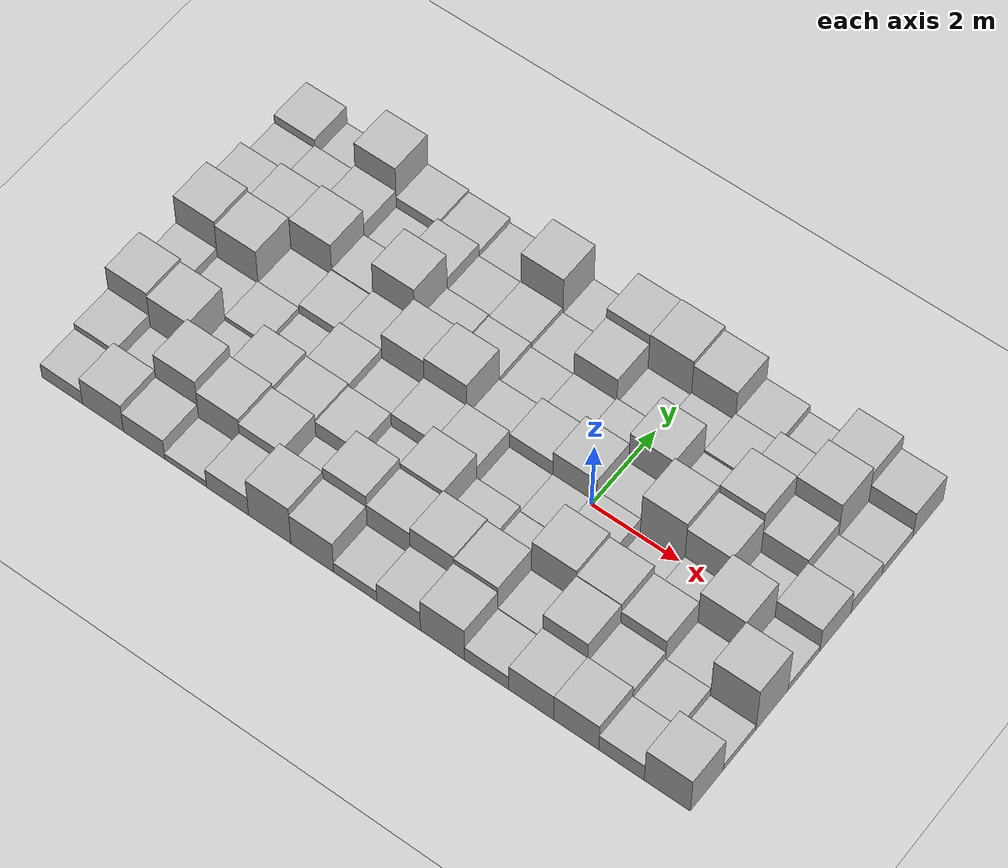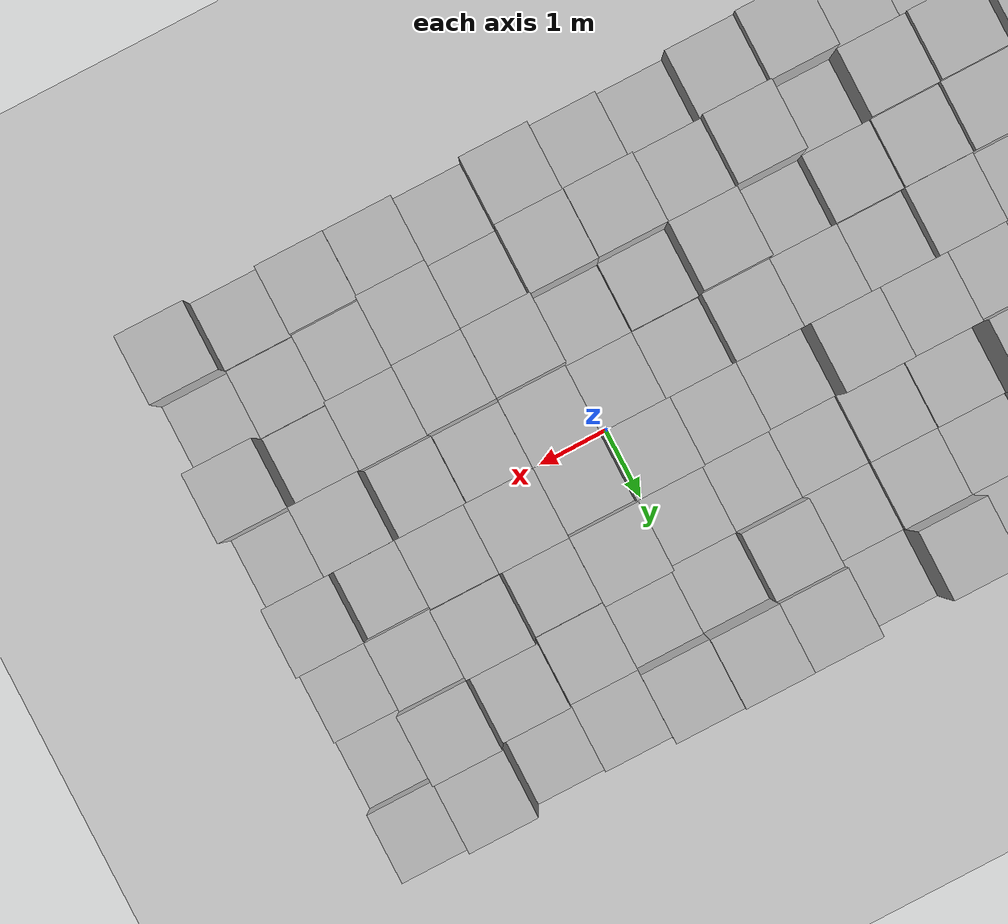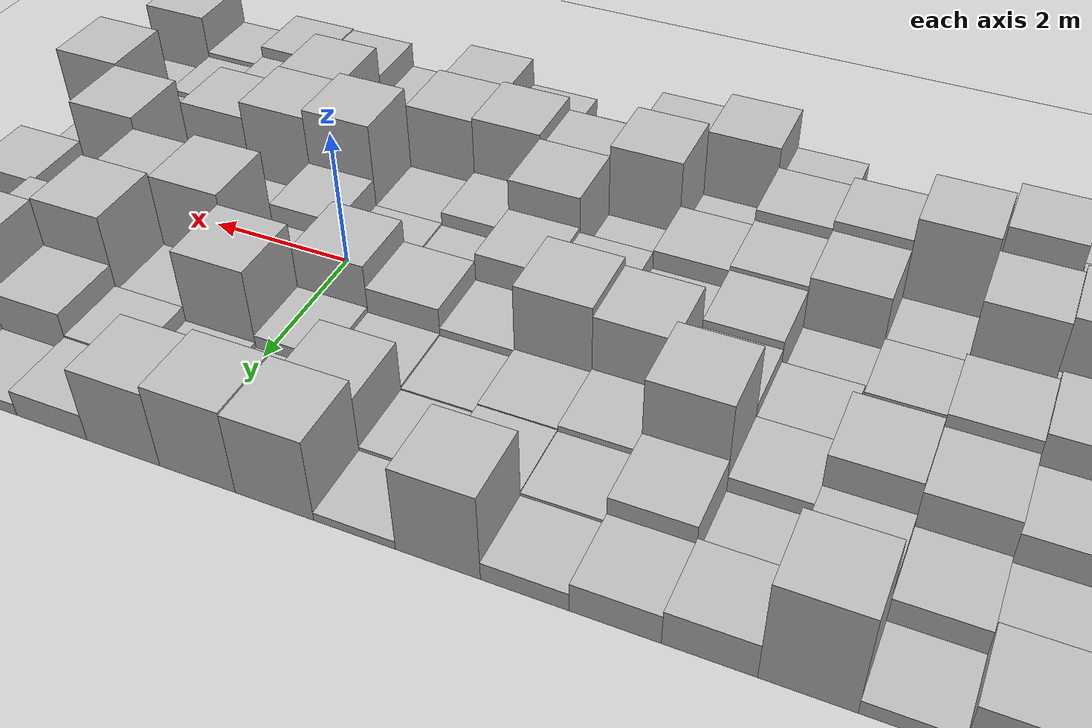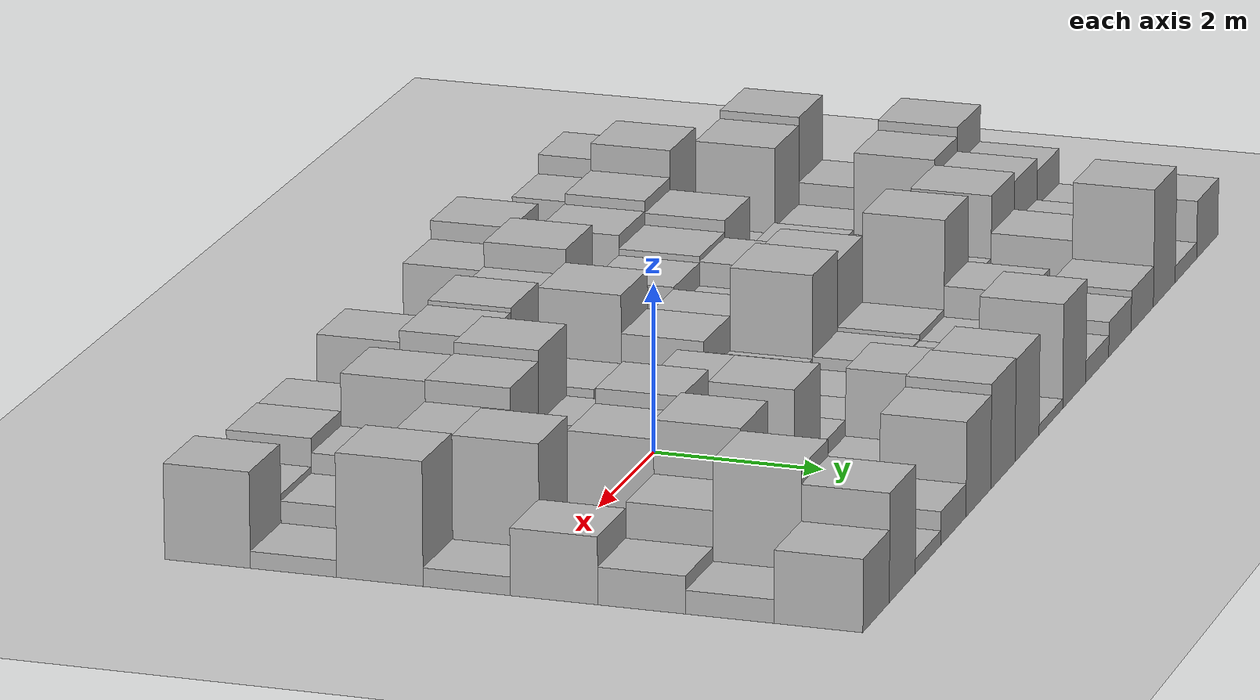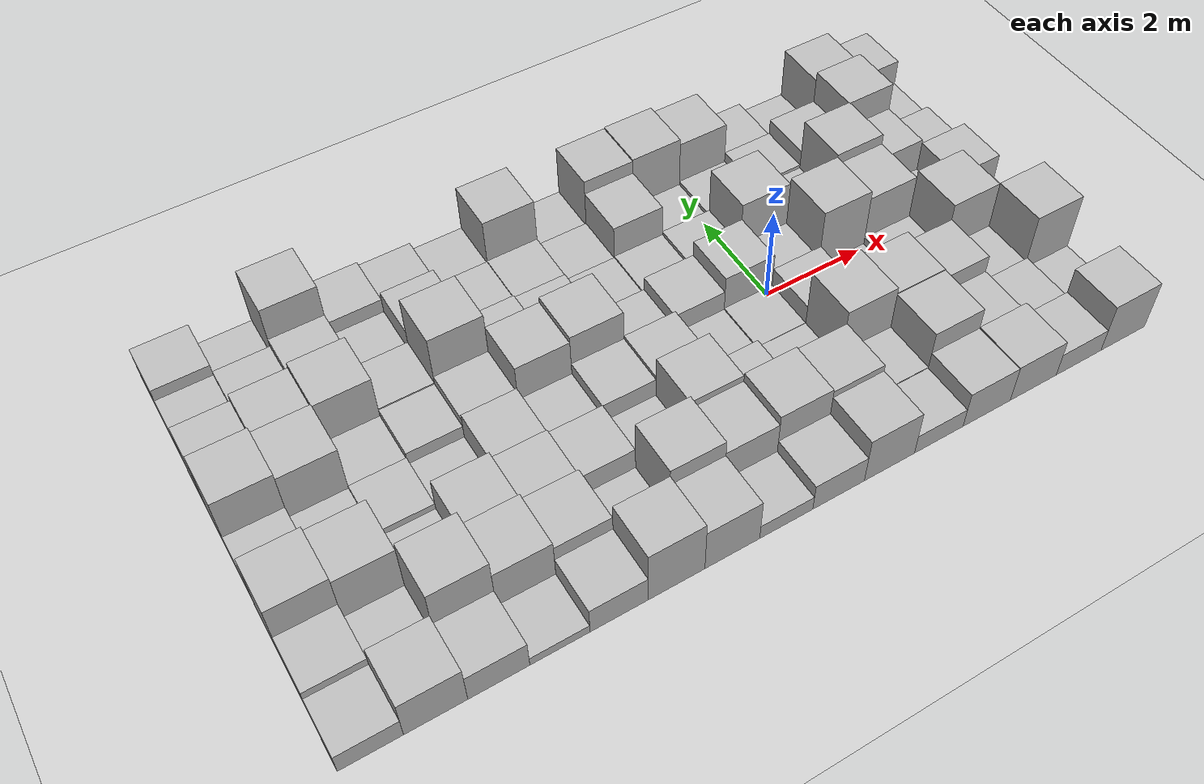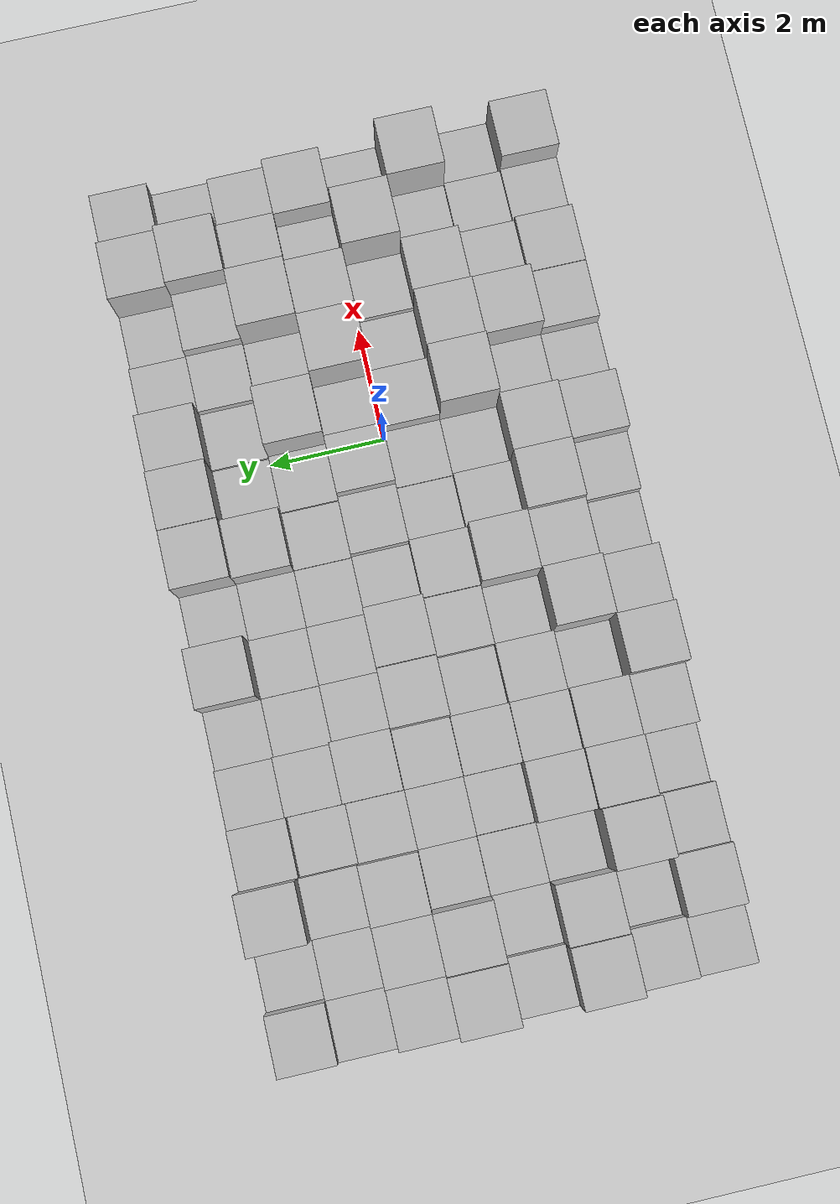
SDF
<?xml version="1.0" ?>
<sdf version="1.6">
    <world name="default">
        <gravity>0 0 -9.81</gravity>
        <include>
            <uri>model://Ground_plane</uri>
        </include>
        <include>
            <uri>model://sun</uri>
        </include>
        <include>
            <uri>model://Generated_terrain</uri>
            <name>Terrain</name>
            <pose>4.6 0 0 0 0 -1.57</pose>
        </include>
    </world>
</sdf>

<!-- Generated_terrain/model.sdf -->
<sdf version='1.6'>
	<model name='Terrain'>
		<static>true</static>
		<link name="box_0_0">
			<pose>-3.5 0.0 0.417745159737 0 0 0</pose>
			<inertial>
				<mass>1.0</mass>
				<inertia>
					<ixx>0.083</ixx>
 					<ixy>0.0</ixy>
   					<ixz>0.0</ixz>
   					<iyy>0.083</iyy>
 					<iyz>0.0</iyz>
   					<izz>0.083</izz>
 				</inertia>
			</inertial>
			<collision name="collision">
				<geometry>
					<box>
						<size>1.0 1.0 0.835490319475</size>
					</box>
				</geometry>
			</collision>
			<visual name="visual">
				<geometry>
					<box>
						<size>1.0 1.0 0.835490319475</size>
					</box>
				</geometry>
			</visual>
		</link>

		<link name="box_0_1">
			<pose>-3.5 -1.0 0.628804138089 0 0 0</pose>
			<inertial>
				<mass>1.0</mass>
				<inertia>
					<ixx>0.083</ixx>
 					<ixy>0.0</ixy>
   					<ixz>0.0</ixz>
   					<iyy>0.083</iyy>
 					<iyz>0.0</iyz>
   					<izz>0.083</izz>
 				</inertia>
			</inertial>
			<collision name="collision">
				<geometry>
					<box>
						<size>1.0 1.0 1.25760827618</size>
					</box>
				</geometry>
			</collision>
			<visual name="visual">
				<geometry>
					<box>
						<size>1.0 1.0 1.25760827618</size>
					</box>
				</geometry>
			</visual>
		</link>

		<link name="box_0_2">
			<pose>-3.5 -2.0 0.0851426585516 0 0 0</pose>
			<inertial>
				<mass>1.0</mass>
				<inertia>
					<ixx>0.083</ixx>
 					<ixy>0.0</ixy>
   					<ixz>0.0</ixz>
   					<iyy>0.083</iyy>
 					<iyz>0.0</iyz>
   					<izz>0.083</izz>
 				</inertia>
			</inertial>
			<collision name="collision">
				<geometry>
					<box>
						<size>1.0 1.0 0.170285317103</size>
					</box>
				</geometry>
			</collision>
			<visual name="visual">
				<geometry>
					<box>
						<size>1.0 1.0 0.170285317103</size>
					</box>
				</geometry>
			</visual>
		</link>

		<link name="box_0_3">
			<pose>-3.5 -3.0 0.195820164618 0 0 0</pose>
			<inertial>
				<mass>1.0</mass>
				<inertia>
					<ixx>0.083</ixx>
 					<ixy>0.0</ixy>
   					<ixz>0.0</ixz>
   					<iyy>0.083</iyy>
 					<iyz>0.0</iyz>
   					<izz>0.083</izz>
 				</inertia>
			</inertial>
			<collision name="collision">
				<geometry>
					<box>
						<size>1.0 1.0 0.391640329236</size>
					</box>
				</geometry>
			</collision>
			<visual name="visual">
				<geometry>
					<box>
						<size>1.0 1.0 0.391640329236</size>
					</box>
				</geometry>
			</visual>
		</link>

		<link name="box_0_4">
			<pose>-3.5 -4.0 0.556168339486 0 0 0</pose>
			<inertial>
				<mass>1.0</mass>
				<inertia>
					<ixx>0.083</ixx>
 					<ixy>0.0</ixy>
   					<ixz>0.0</ixz>
   					<iyy>0.083</iyy>
 					<iyz>0.0</iyz>
   					<izz>0.083</izz>
 				</inertia>
			</inertial>
			<collision name="collision">
				<geometry>
					<box>
						<size>1.0 1.0 1.11233667897</size>
					</box>
				</geometry>
			</collision>
			<visual name="visual">
				<geometry>
					<box>
						<size>1.0 1.0 1.11233667897</size>
					</box>
				</geometry>
			</visual>
		</link>

		<link name="box_0_5">
			<pose>-3.5 -5.0 0.619294533796 0 0 0</pose>
			<inertial>
				<mass>1.0</mass>
				<inertia>
					<ixx>0.083</ixx>
 					<ixy>0.0</ixy>
   					<ixz>0.0</ixz>
   					<iyy>0.083</iyy>
 					<iyz>0.0</iyz>
   					<izz>0.083</izz>
 				</inertia>
			</inertial>
			<collision name="collision">
				<geometry>
					<box>
						<size>1.0 1.0 1.23858906759</size>
					</box>
				</geometry>
			</collision>
			<visual name="visual">
				<geometry>
					<box>
						<size>1.0 1.0 1.23858906759</size>
					</box>
				</geometry>
			</visual>
		</link>

		<link name="box_0_6">
			<pose>-3.5 -6.0 0.604735536653 0 0 0</pose>
			<inertial>
				<mass>1.0</mass>
				<inertia>
					<ixx>0.083</ixx>
 					<ixy>0.0</ixy>
   					<ixz>0.0</ixz>
   					<iyy>0.083</iyy>
 					<iyz>0.0</iyz>
   					<izz>0.083</izz>
 				</inertia>
			</inertial>
			<collision name="collision">
				<geometry>
					<box>
						<size>1.0 1.0 1.20947107331</size>
					</box>
				</geometry>
			</collision>
			<visual name="visual">
				<geometry>
					<box>
						<size>1.0 1.0 1.20947107331</size>
					</box>
				</geometry>
			</visual>
		</link>

		<link name="box_0_7">
			<pose>-3.5 -7.0 0.0607612955176 0 0 0</pose>
			<inertial>
				<mass>1.0</mass>
				<inertia>
					<ixx>0.083</ixx>
 					<ixy>0.0</ixy>
   					<ixz>0.0</ixz>
   					<iyy>0.083</iyy>
 					<iyz>0.0</iyz>
   					<izz>0.083</izz>
 				</inertia>
			</inertial>
			<collision name="collision">
				<geometry>
					<box>
						<size>1.0 1.0 0.121522591035</size>
					</box>
				</geometry>
			</collision>
			<visual name="visual">
				<geometry>
					<box>
						<size>1.0 1.0 0.121522591035</size>
					</box>
				</geometry>
			</visual>
		</link>

		<link name="box_0_8">
			<pose>-3.5 -8.0 0.630093040695 0 0 0</pose>
			<inertial>
				<mass>1.0</mass>
				<inertia>
					<ixx>0.083</ixx>
 					<ixy>0.0</ixy>
   					<ixz>0.0</ixz>
   					<iyy>0.083</iyy>
 					<iyz>0.0</iyz>
   					<izz>0.083</izz>
 				</inertia>
			</inertial>
			<collision name="collision">
				<geometry>
					<box>
						<size>1.0 1.0 1.26018608139</size>
					</box>
				</geometry>
			</collision>
			<visual name="visual">
				<geometry>
					<box>
						<size>1.0 1.0 1.26018608139</size>
					</box>
				</geometry>
			</visual>
		</link>

		<link name="box_0_9">
			<pose>-3.5 -9.0 0.132783228985 0 0 0</pose>
			<inertial>
				<mass>1.0</mass>
				<inertia>
					<ixx>0.083</ixx>
 					<ixy>0.0</ixy>
   					<ixz>0.0</ixz>
   					<iyy>0.083</iyy>
 					<iyz>0.0</iyz>
   					<izz>0.083</izz>
 				</inertia>
			</inertial>
			<collision name="collision">
				<geometry>
					<box>
						<size>1.0 1.0 0.26556645797</size>
					</box>
				</geometry>
			</collision>
			<visual name="visual">
				<geometry>
					<box>
						<size>1.0 1.0 0.26556645797</size>
					</box>
				</geometry>
			</visual>
		</link>

		<link name="box_0_10">
			<pose>-3.5 -10.0 0.214963397513 0 0 0</pose>
			<inertial>
				<mass>1.0</mass>
				<inertia>
					<ixx>0.083</ixx>
 					<ixy>0.0</ixy>
   					<ixz>0.0</ixz>
   					<iyy>0.083</iyy>
 					<iyz>0.0</iyz>
   					<izz>0.083</izz>
 				</inertia>
			</inertial>
			<collision name="collision">
				<geometry>
					<box>
						<size>1.0 1.0 0.429926795026</size>
					</box>
				</geometry>
			</collision>
			<visual name="visual">
				<geometry>
					<box>
						<size>1.0 1.0 0.429926795026</size>
					</box>
				</geometry>
			</visual>
		</link>

		<link name="box_0_11">
			<pose>-3.5 -11.0 0.255203327798 0 0 0</pose>
			<inertial>
				<mass>1.0</mass>
				<inertia>
					<ixx>0.083</ixx>
 					<ixy>0.0</ixy>
   					<ixz>0.0</ixz>
   					<iyy>0.083</iyy>
 					<iyz>0.0</iyz>
   					<izz>0.083</izz>
 				</inertia>
			</inertial>
			<collision name="collision">
				<geometry>
					<box>
						<size>1.0 1.0 0.510406655596</size>
					</box>
				</geometry>
			</collision>
			<visual name="visual">
				<geometry>
					<box>
						<size>1.0 1.0 0.510406655596</size>
					</box>
				</geometry>
			</visual>
		</link>

		<link name="box_0_12">
			<pose>-3.5 -12.0 0.726490676676 0 0 0</pose>
			<inertial>
				<mass>1.0</mass>
				<inertia>
					<ixx>0.083</ixx>
 					<ixy>0.0</ixy>
   					<ixz>0.0</ixz>
   					<iyy>0.083</iyy>
 					<iyz>0.0</iyz>
   					<izz>0.083</izz>
 				</inertia>
			</inertial>
			<collision name="collision">
				<geometry>
					<box>
						<size>1.0 1.0 1.45298135335</size>
					</box>
				</geometry>
			</collision>
			<visual name="visual">
				<geometry>
					<box>
						<size>1.0 1.0 1.45298135335</size>
					</box>
				</geometry>
			</visual>
		</link>

		<link name="box_0_13">
			<pose>-3.5 -13.0 0.10314080423 0 0 0</pose>
			<inertial>
				<mass>1.0</mass>
				<inertia>
					<ixx>0.083</ixx>
 					<ixy>0.0</ixy>
   					<ixz>0.0</ixz>
   					<iyy>0.083</iyy>
 					<iyz>0.0</iyz>
   					<izz>0.083</izz>
 				</inertia>
			</inertial>
			<collision name="collision">
				<geometry>
					<box>
						<size>1.0 1.0 0.206281608459</size>
					</box>
				</geometry>
			</collision>
			<visual name="visual">
				<geometry>
					<box>
						<size>1.0 1.0 0.206281608459</size>
					</box>
				</geometry>
			</visual>
		</link>

		<link name="box_0_14">
			<pose>-3.5 -14.0 0.362036572515 0 0 0</pose>
			<inertial>
				<mass>1.0</mass>
				<inertia>
					<ixx>0.083</ixx>
 					<ixy>0.0</ixy>
   					<ixz>0.0</ixz>
   					<iyy>0.083</iyy>
 					<iyz>0.0</iyz>
   					<izz>0.083</izz>
 				</inertia>
			</inertial>
			<collision name="collision">
				<geometry>
					<box>
						<size>1.0 1.0 0.724073145029</size>
					</box>
				</geometry>
			</collision>
			<visual name="visual">
				<geometry>
					<box>
						<size>1.0 1.0 0.724073145029</size>
					</box>
				</geometry>
			</visual>
		</link>

		<link name="box_1_0">
			<pose>-2.5 0.0 0.13550543962 0 0 0</pose>
			<inertial>
				<mass>1.0</mass>
				<inertia>
					<ixx>0.083</ixx>
 					<ixy>0.0</ixy>
   					<ixz>0.0</ixz>
   					<iyy>0.083</iyy>
 					<iyz>0.0</iyz>
   					<izz>0.083</izz>
 				</inertia>
			</inertial>
			<collision name="collision">
				<geometry>
					<box>
						<size>1.0 1.0 0.27101087924</size>
					</box>
				</geometry>
			</collision>
			<visual name="visual">
				<geometry>
					<box>
						<size>1.0 1.0 0.27101087924</size>
					</box>
				</geometry>
			</visual>
		</link>

		<link name="box_1_1">
			<pose>-2.5 -1.0 0.726013910653 0 0 0</pose>
			<inertial>
				<mass>1.0</mass>
				<inertia>
					<ixx>0.083</ixx>
 					<ixy>0.0</ixy>
   					<ixz>0.0</ixz>
   					<iyy>0.083</iyy>
 					<iyz>0.0</iyz>
   					<izz>0.083</izz>
 				</inertia>
			</inertial>
			<collision name="collision">
				<geometry>
					<box>
						<size>1.0 1.0 1.45202782131</size>
					</box>
				</geometry>
			</collision>
			<visual name="visual">
				<geometry>
					<box>
						<size>1.0 1.0 1.45202782131</size>
					</box>
				</geometry>
			</visual>
		</link>

		<link name="box_1_2">
			<pose>-2.5 -2.0 0.375129767033 0 0 0</pose>
			<inertial>
				<mass>1.0</mass>
				<inertia>
					<ixx>0.083</ixx>
 					<ixy>0.0</ixy>
   					<ixz>0.0</ixz>
   					<iyy>0.083</iyy>
 					<iyz>0.0</iyz>
   					<izz>0.083</izz>
 				</inertia>
			</inertial>
			<collision name="collision">
				<geometry>
					<box>
						<size>1.0 1.0 0.750259534066</size>
					</box>
				</geometry>
			</collision>
			<visual name="visual">
				<geometry>
					<box>
						<size>1.0 1.0 0.750259534066</size>
					</box>
				</geometry>
			</visual>
		</link>

		<link name="box_1_3">
			<pose>-2.5 -3.0 0.208997817152 0 0 0</pose>
			<inertial>
				<mass>1.0</mass>
				<inertia>
					<ixx>0.083</ixx>
 					<ixy>0.0</ixy>
   					<ixz>0.0</ixz>
   					<iyy>0.083</iyy>
 					<iyz>0.0</iyz>
   					<izz>0.083</izz>
 				</inertia>
			</inertial>
			<collision name="collision">
				<geometry>
					<box>
						<size>1.0 1.0 0.417995634303</size>
					</box>
				</geometry>
			</collision>
			<visual name="visual">
				<geometry>
					<box>
						<size>1.0 1.0 0.417995634303</size>
					</box>
				</geometry>
			</visual>
		</link>

		<link name="box_1_4">
			<pose>-2.5 -4.0 0.0964454472175 0 0 0</pose>
			<inertial>
				<mass>1.0</mass>
				<inertia>
					<ixx>0.083</ixx>
 					<ixy>0.0</ixy>
   					<ixz>0.0</ixz>
   					<iyy>0.083</iyy>
 					<iyz>0.0</iyz>
   					<izz>0.083</izz>
 				</inertia>
			</inertial>
			<collision name="collision">
				<geometry>
					<box>
						<size>1.0 1.0 0.192890894435</size>
					</box>
				</geometry>
			</collision>
			<visual name="visual">
				<geometry>
					<box>
						<size>1.0 1.0 0.192890894435</size>
					</box>
				</geometry>
			</visual>
		</link>

		<link name="box_1_5">
			<pose>-2.5 -5.0 0.0562978745284 0 0 0</pose>
			<inertial>
				<mass>1.0</mass>
				<inertia>
					<ixx>0.083</ixx>
 					<ixy>0.0</ixy>
   					<ixz>0.0</ixz>
   					<iyy>0.083</iyy>
 					<iyz>0.0</iyz>
   					<izz>0.083</izz>
 				</inertia>
			</inertial>
			<collision name="collision">
				<geometry>
					<box>
						<size>1.0 1.0 0.112595749057</size>
					</box>
				</geometry>
			</collision>
			<visual name="visual">
				<geometry>
					<box>
						<size>1.0 1.0 0.112595749057</size>
					</box>
				</geometry>
			</visual>
		</link>

		<link name="box_1_6">
			<pose>-2.5 -6.0 0.460396959695 0 0 0</pose>
			<inertial>
				<mass>1.0</mass>
				<inertia>
					<ixx>0.083</ixx>
 					<ixy>0.0</ixy>
   					<ixz>0.0</ixz>
   					<iyy>0.083</iyy>
 					<iyz>0.0</iyz>
   					<izz>0.083</izz>
 				</inertia>
			</inertial>
			<collision name="collision">
				<geometry>
					<box>
						<size>1.0 1.0 0.920793919391</size>
					</box>
				</geometry>
			</collision>
			<visual name="visual">
				<geometry>
					<box>
						<size>1.0 1.0 0.920793919391</size>
					</box>
				</geometry>
			</visual>
		</link>

		<link name="box_1_7">
			<pose>-2.5 -7.0 0.0869456284371 0 0 0</pose>
			<inertial>
				<mass>1.0</mass>
				<inertia>
					<ixx>0.083</ixx>
 					<ixy>0.0</ixy>
   					<ixz>0.0</ixz>
   					<iyy>0.083</iyy>
 					<iyz>0.0</iyz>
   					<izz>0.083</izz>
 				</inertia>
			</inertial>
			<collision name="collision">
				<geometry>
					<box>
						<size>1.0 1.0 0.173891256874</size>
					</box>
				</geometry>
			</collision>
			<visual name="visual">
				<geometry>
					<box>
						<size>1.0 1.0 0.173891256874</size>
					</box>
				</geometry>
			</visual>
		</link>

		<link name="box_1_8">
			<pose>-2.5 -8.0 0.161309622204 0 0 0</pose>
			<inertial>
				<mass>1.0</mass>
				<inertia>
					<ixx>0.083</ixx>
 					<ixy>0.0</ixy>
   					<ixz>0.0</ixz>
   					<iyy>0.083</iyy>
 					<iyz>0.0</iyz>
   					<izz>0.083</izz>
 				</inertia>
			</inertial>
			<collision name="collision">
				<geometry>
					<box>
						<size>1.0 1.0 0.322619244408</size>
					</box>
				</geometry>
			</collision>
			<visual name="visual">
				<geometry>
					<box>
						<size>1.0 1.0 0.322619244408</size>
					</box>
				</geometry>
			</visual>
		</link>

		<link name="box_1_9">
			<pose>-2.5 -9.0 0.152661184607 0 0 0</pose>
			<inertial>
				<mass>1.0</mass>
				<inertia>
					<ixx>0.083</ixx>
 					<ixy>0.0</ixy>
   					<ixz>0.0</ixz>
   					<iyy>0.083</iyy>
 					<iyz>0.0</iyz>
   					<izz>0.083</izz>
 				</inertia>
			</inertial>
			<collision name="collision">
				<geometry>
					<box>
						<size>1.0 1.0 0.305322369214</size>
					</box>
				</geometry>
			</collision>
			<visual name="visual">
				<geometry>
					<box>
						<size>1.0 1.0 0.305322369214</size>
					</box>
				</geometry>
			</visual>
		</link>

		<link name="box_1_10">
			<pose>-2.5 -10.0 0.341582008617 0 0 0</pose>
			<inertial>
				<mass>1.0</mass>
				<inertia>
					<ixx>0.083</ixx>
 					<ixy>0.0</ixy>
   					<ixz>0.0</ixz>
   					<iyy>0.083</iyy>
 					<iyz>0.0</iyz>
   					<izz>0.083</izz>
 				</inertia>
			</inertial>
			<collision name="collision">
				<geometry>
					<box>
						<size>1.0 1.0 0.683164017234</size>
					</box>
				</geometry>
			</collision>
			<visual name="visual">
				<geometry>
					<box>
						<size>1.0 1.0 0.683164017234</size>
					</box>
				</geometry>
			</visual>
		</link>

		<link name="box_1_11">
			<pose>-2.5 -11.0 0.0978201423521 0 0 0</pose>
			<inertial>
				<mass>1.0</mass>
				<inertia>
					<ixx>0.083</ixx>
 					<ixy>0.0</ixy>
   					<ixz>0.0</ixz>
   					<iyy>0.083</iyy>
 					<iyz>0.0</iyz>
   					<izz>0.083</izz>
 				</inertia>
			</inertial>
			<collision name="collision">
				<geometry>
					<box>
						<size>1.0 1.0 0.195640284704</size>
					</box>
				</geometry>
			</collision>
			<visual name="visual">
				<geometry>
					<box>
						<size>1.0 1.0 0.195640284704</size>
					</box>
				</geometry>
			</visual>
		</link>

		<link name="box_1_12">
			<pose>-2.5 -12.0 0.367014219254 0 0 0</pose>
			<inertial>
				<mass>1.0</mass>
				<inertia>
					<ixx>0.083</ixx>
 					<ixy>0.0</ixy>
   					<ixz>0.0</ixz>
   					<iyy>0.083</iyy>
 					<iyz>0.0</iyz>
   					<izz>0.083</izz>
 				</inertia>
			</inertial>
			<collision name="collision">
				<geometry>
					<box>
						<size>1.0 1.0 0.734028438509</size>
					</box>
				</geometry>
			</collision>
			<visual name="visual">
				<geometry>
					<box>
						<size>1.0 1.0 0.734028438509</size>
					</box>
				</geometry>
			</visual>
		</link>

		<link name="box_1_13">
			<pose>-2.5 -13.0 0.279296993047 0 0 0</pose>
			<inertial>
				<mass>1.0</mass>
				<inertia>
					<ixx>0.083</ixx>
 					<ixy>0.0</ixy>
   					<ixz>0.0</ixz>
   					<iyy>0.083</iyy>
 					<iyz>0.0</iyz>
   					<izz>0.083</izz>
 				</inertia>
			</inertial>
			<collision name="collision">
				<geometry>
					<box>
						<size>1.0 1.0 0.558593986095</size>
					</box>
				</geometry>
			</collision>
			<visual name="visual">
				<geometry>
					<box>
						<size>1.0 1.0 0.558593986095</size>
					</box>
				</geometry>
			</visual>
		</link>

		<link name="box_1_14">
			<pose>-2.5 -14.0 0.235284861385 0 0 0</pose>
			<inertial>
				<mass>1.0</mass>
				<inertia>
					<ixx>0.083</ixx>
 					<ixy>0.0</ixy>
   					<ixz>0.0</ixz>
   					<iyy>0.083</iyy>
 					<iyz>0.0</iyz>
   					<izz>0.083</izz>
 				</inertia>
			</inertial>
			<collision name="collision">
				<geometry>
					<box>
						<size>1.0 1.0 0.47056972277</size>
					</box>
				</geometry>
			</collision>
			<visual name="visual">
				<geometry>
					<box>
						<size>1.0 1.0 0.47056972277</size>
					</box>
				</geometry>
			</visual>
		</link>

		<link name="box_2_0">
			<pose>-1.5 0.0 0.216664329808 0 0 0</pose>
			<inertial>
				<mass>1.0</mass>
				<inertia>
					<ixx>0.083</ixx>
 					<ixy>0.0</ixy>
   					<ixz>0.0</ixz>
   					<iyy>0.083</iyy>
 					<iyz>0.0</iyz>
   					<izz>0.083</izz>
 				</inertia>
			</inertial>
			<collision name="collision">
				<geometry>
					<box>
						<size>1.0 1.0 0.433328659617</size>
					</box>
				</geometry>
			</collision>
			<visual name="visual">
				<geometry>
					<box>
						<size>1.0 1.0 0.433328659617</size>
					</box>
				</geometry>
			</visual>
		</link>

		<link name="box_2_1">
			<pose>-1.5 -1.0 0.426060375249 0 0 0</pose>
			<inertial>
				<mass>1.0</mass>
				<inertia>
					<ixx>0.083</ixx>
 					<ixy>0.0</ixy>
   					<ixz>0.0</ixz>
   					<iyy>0.083</iyy>
 					<iyz>0.0</iyz>
   					<izz>0.083</izz>
 				</inertia>
			</inertial>
			<collision name="collision">
				<geometry>
					<box>
						<size>1.0 1.0 0.852120750499</size>
					</box>
				</geometry>
			</collision>
			<visual name="visual">
				<geometry>
					<box>
						<size>1.0 1.0 0.852120750499</size>
					</box>
				</geometry>
			</visual>
		</link>

		<link name="box_2_2">
			<pose>-1.5 -2.0 0.738666099266 0 0 0</pose>
			<inertial>
				<mass>1.0</mass>
				<inertia>
					<ixx>0.083</ixx>
 					<ixy>0.0</ixy>
   					<ixz>0.0</ixz>
   					<iyy>0.083</iyy>
 					<iyz>0.0</iyz>
   					<izz>0.083</izz>
 				</inertia>
			</inertial>
			<collision name="collision">
				<geometry>
					<box>
						<size>1.0 1.0 1.47733219853</size>
					</box>
				</geometry>
			</collision>
			<visual name="visual">
				<geometry>
					<box>
						<size>1.0 1.0 1.47733219853</size>
					</box>
				</geometry>
			</visual>
		</link>

		<link name="box_2_3">
			<pose>-1.5 -3.0 0.172789882983 0 0 0</pose>
			<inertial>
				<mass>1.0</mass>
				<inertia>
					<ixx>0.083</ixx>
 					<ixy>0.0</ixy>
   					<ixz>0.0</ixz>
   					<iyy>0.083</iyy>
 					<iyz>0.0</iyz>
   					<izz>0.083</izz>
 				</inertia>
			</inertial>
			<collision name="collision">
				<geometry>
					<box>
						<size>1.0 1.0 0.345579765965</size>
					</box>
				</geometry>
			</collision>
			<visual name="visual">
				<geometry>
					<box>
						<size>1.0 1.0 0.345579765965</size>
					</box>
				</geometry>
			</visual>
		</link>

		<link name="box_2_4">
			<pose>-1.5 -4.0 0.645655087552 0 0 0</pose>
			<inertial>
				<mass>1.0</mass>
				<inertia>
					<ixx>0.083</ixx>
 					<ixy>0.0</ixy>
   					<ixz>0.0</ixz>
   					<iyy>0.083</iyy>
 					<iyz>0.0</iyz>
   					<izz>0.083</izz>
 				</inertia>
			</inertial>
			<collision name="collision">
				<geometry>
					<box>
						<size>1.0 1.0 1.2913101751</size>
					</box>
				</geometry>
			</collision>
			<visual name="visual">
				<geometry>
					<box>
						<size>1.0 1.0 1.2913101751</size>
					</box>
				</geometry>
			</visual>
		</link>

		<link name="box_2_5">
			<pose>-1.5 -5.0 0.151310680941 0 0 0</pose>
			<inertial>
				<mass>1.0</mass>
				<inertia>
					<ixx>0.083</ixx>
 					<ixy>0.0</ixy>
   					<ixz>0.0</ixz>
   					<iyy>0.083</iyy>
 					<iyz>0.0</iyz>
   					<izz>0.083</izz>
 				</inertia>
			</inertial>
			<collision name="collision">
				<geometry>
					<box>
						<size>1.0 1.0 0.302621361882</size>
					</box>
				</geometry>
			</collision>
			<visual name="visual">
				<geometry>
					<box>
						<size>1.0 1.0 0.302621361882</size>
					</box>
				</geometry>
			</visual>
		</link>

		<link name="box_2_6">
			<pose>-1.5 -6.0 0.1122067063 0 0 0</pose>
			<inertial>
				<mass>1.0</mass>
				<inertia>
					<ixx>0.083</ixx>
 					<ixy>0.0</ixy>
   					<ixz>0.0</ixz>
   					<iyy>0.083</iyy>
 					<iyz>0.0</iyz>
   					<izz>0.083</izz>
 				</inertia>
			</inertial>
			<collision name="collision">
				<geometry>
					<box>
						<size>1.0 1.0 0.224413412601</size>
					</box>
				</geometry>
			</collision>
			<visual name="visual">
				<geometry>
					<box>
						<size>1.0 1.0 0.224413412601</size>
					</box>
				</geometry>
			</visual>
		</link>

		<link name="box_2_7">
			<pose>-1.5 -7.0 0.0967583786873 0 0 0</pose>
			<inertial>
				<mass>1.0</mass>
				<inertia>
					<ixx>0.083</ixx>
 					<ixy>0.0</ixy>
   					<ixz>0.0</ixz>
   					<iyy>0.083</iyy>
 					<iyz>0.0</iyz>
   					<izz>0.083</izz>
 				</inertia>
			</inertial>
			<collision name="collision">
				<geometry>
					<box>
						<size>1.0 1.0 0.193516757375</size>
					</box>
				</geometry>
			</collision>
			<visual name="visual">
				<geometry>
					<box>
						<size>1.0 1.0 0.193516757375</size>
					</box>
				</geometry>
			</visual>
		</link>

		<link name="box_2_8">
			<pose>-1.5 -8.0 0.169127132474 0 0 0</pose>
			<inertial>
				<mass>1.0</mass>
				<inertia>
					<ixx>0.083</ixx>
 					<ixy>0.0</ixy>
   					<ixz>0.0</ixz>
   					<iyy>0.083</iyy>
 					<iyz>0.0</iyz>
   					<izz>0.083</izz>
 				</inertia>
			</inertial>
			<collision name="collision">
				<geometry>
					<box>
						<size>1.0 1.0 0.338254264948</size>
					</box>
				</geometry>
			</collision>
			<visual name="visual">
				<geometry>
					<box>
						<size>1.0 1.0 0.338254264948</size>
					</box>
				</geometry>
			</visual>
		</link>

		<link name="box_2_9">
			<pose>-1.5 -9.0 0.194800044003 0 0 0</pose>
			<inertial>
				<mass>1.0</mass>
				<inertia>
					<ixx>0.083</ixx>
 					<ixy>0.0</ixy>
   					<ixz>0.0</ixz>
   					<iyy>0.083</iyy>
 					<iyz>0.0</iyz>
   					<izz>0.083</izz>
 				</inertia>
			</inertial>
			<collision name="collision">
				<geometry>
					<box>
						<size>1.0 1.0 0.389600088005</size>
					</box>
				</geometry>
			</collision>
			<visual name="visual">
				<geometry>
					<box>
						<size>1.0 1.0 0.389600088005</size>
					</box>
				</geometry>
			</visual>
		</link>

		<link name="box_2_10">
			<pose>-1.5 -10.0 0.743552029229 0 0 0</pose>
			<inertial>
				<mass>1.0</mass>
				<inertia>
					<ixx>0.083</ixx>
 					<ixy>0.0</ixy>
   					<ixz>0.0</ixz>
   					<iyy>0.083</iyy>
 					<iyz>0.0</iyz>
   					<izz>0.083</izz>
 				</inertia>
			</inertial>
			<collision name="collision">
				<geometry>
					<box>
						<size>1.0 1.0 1.48710405846</size>
					</box>
				</geometry>
			</collision>
			<visual name="visual">
				<geometry>
					<box>
						<size>1.0 1.0 1.48710405846</size>
					</box>
				</geometry>
			</visual>
		</link>

		<link name="box_2_11">
			<pose>-1.5 -11.0 0.207563838125 0 0 0</pose>
			<inertial>
				<mass>1.0</mass>
				<inertia>
					<ixx>0.083</ixx>
 					<ixy>0.0</ixy>
   					<ixz>0.0</ixz>
   					<iyy>0.083</iyy>
 					<iyz>0.0</iyz>
   					<izz>0.083</izz>
 				</inertia>
			</inertial>
			<collision name="collision">
				<geometry>
					<box>
						<size>1.0 1.0 0.41512767625</size>
					</box>
				</geometry>
			</collision>
			<visual name="visual">
				<geometry>
					<box>
						<size>1.0 1.0 0.41512767625</size>
					</box>
				</geometry>
			</visual>
		</link>

		<link name="box_2_12">
			<pose>-1.5 -12.0 0.598522405695 0 0 0</pose>
			<inertial>
				<mass>1.0</mass>
				<inertia>
					<ixx>0.083</ixx>
 					<ixy>0.0</ixy>
   					<ixz>0.0</ixz>
   					<iyy>0.083</iyy>
 					<iyz>0.0</iyz>
   					<izz>0.083</izz>
 				</inertia>
			</inertial>
			<collision name="collision">
				<geometry>
					<box>
						<size>1.0 1.0 1.19704481139</size>
					</box>
				</geometry>
			</collision>
			<visual name="visual">
				<geometry>
					<box>
						<size>1.0 1.0 1.19704481139</size>
					</box>
				</geometry>
			</visual>
		</link>

		<link name="box_2_13">
			<pose>-1.5 -13.0 0.539018685183 0 0 0</pose>
			<inertial>
				<mass>1.0</mass>
				<inertia>
					<ixx>0.083</ixx>
 					<ixy>0.0</ixy>
   					<ixz>0.0</ixz>
   					<iyy>0.083</iyy>
 					<iyz>0.0</iyz>
   					<izz>0.083</izz>
 				</inertia>
			</inertial>
			<collision name="collision">
				<geometry>
					<box>
						<size>1.0 1.0 1.07803737037</size>
					</box>
				</geometry>
			</collision>
			<visual name="visual">
				<geometry>
					<box>
						<size>1.0 1.0 1.07803737037</size>
					</box>
				</geometry>
			</visual>
		</link>

		<link name="box_2_14">
			<pose>-1.5 -14.0 0.457222023088 0 0 0</pose>
			<inertial>
				<mass>1.0</mass>
				<inertia>
					<ixx>0.083</ixx>
 					<ixy>0.0</ixy>
   					<ixz>0.0</ixz>
   					<iyy>0.083</iyy>
 					<iyz>0.0</iyz>
   					<izz>0.083</izz>
 				</inertia>
			</inertial>
			<collision name="collision">
				<geometry>
					<box>
						<size>1.0 1.0 0.914444046175</size>
					</box>
				</geometry>
			</collision>
			<visual name="visual">
				<geometry>
					<box>
						<size>1.0 1.0 0.914444046175</size>
					</box>
				</geometry>
			</visual>
		</link>

		<link name="box_3_0">
			<pose>-0.5 0.0 0.389048587632 0 0 0</pose>
			<inertial>
				<mass>1.0</mass>
				<inertia>
					<ixx>0.083</ixx>
 					<ixy>0.0</ixy>
   					<ixz>0.0</ixz>
   					<iyy>0.083</iyy>
 					<iyz>0.0</iyz>
   					<izz>0.083</izz>
 				</inertia>
			</inertial>
			<collision name="collision">
				<geometry>
					<box>
						<size>1.0 1.0 0.778097175265</size>
					</box>
				</geometry>
			</collision>
			<visual name="visual">
				<geometry>
					<box>
						<size>1.0 1.0 0.778097175265</size>
					</box>
				</geometry>
			</visual>
		</link>

		<link name="box_3_1">
			<pose>-0.5 -1.0 0.05966804592 0 0 0</pose>
			<inertial>
				<mass>1.0</mass>
				<inertia>
					<ixx>0.083</ixx>
 					<ixy>0.0</ixy>
   					<ixz>0.0</ixz>
   					<iyy>0.083</iyy>
 					<iyz>0.0</iyz>
   					<izz>0.083</izz>
 				</inertia>
			</inertial>
			<collision name="collision">
				<geometry>
					<box>
						<size>1.0 1.0 0.11933609184</size>
					</box>
				</geometry>
			</collision>
			<visual name="visual">
				<geometry>
					<box>
						<size>1.0 1.0 0.11933609184</size>
					</box>
				</geometry>
			</visual>
		</link>

		<link name="box_3_2">
			<pose>-0.5 -2.0 0.626262475751 0 0 0</pose>
			<inertial>
				<mass>1.0</mass>
				<inertia>
					<ixx>0.083</ixx>
 					<ixy>0.0</ixy>
   					<ixz>0.0</ixz>
   					<iyy>0.083</iyy>
 					<iyz>0.0</iyz>
   					<izz>0.083</izz>
 				</inertia>
			</inertial>
			<collision name="collision">
				<geometry>
					<box>
						<size>1.0 1.0 1.2525249515</size>
					</box>
				</geometry>
			</collision>
			<visual name="visual">
				<geometry>
					<box>
						<size>1.0 1.0 1.2525249515</size>
					</box>
				</geometry>
			</visual>
		</link>

		<link name="box_3_3">
			<pose>-0.5 -3.0 0.714838587176 0 0 0</pose>
			<inertial>
				<mass>1.0</mass>
				<inertia>
					<ixx>0.083</ixx>
 					<ixy>0.0</ixy>
   					<ixz>0.0</ixz>
   					<iyy>0.083</iyy>
 					<iyz>0.0</iyz>
   					<izz>0.083</izz>
 				</inertia>
			</inertial>
			<collision name="collision">
				<geometry>
					<box>
						<size>1.0 1.0 1.42967717435</size>
					</box>
				</geometry>
			</collision>
			<visual name="visual">
				<geometry>
					<box>
						<size>1.0 1.0 1.42967717435</size>
					</box>
				</geometry>
			</visual>
		</link>

		<link name="box_3_4">
			<pose>-0.5 -4.0 0.15687675474 0 0 0</pose>
			<inertial>
				<mass>1.0</mass>
				<inertia>
					<ixx>0.083</ixx>
 					<ixy>0.0</ixy>
   					<ixz>0.0</ixz>
   					<iyy>0.083</iyy>
 					<iyz>0.0</iyz>
   					<izz>0.083</izz>
 				</inertia>
			</inertial>
			<collision name="collision">
				<geometry>
					<box>
						<size>1.0 1.0 0.313753509479</size>
					</box>
				</geometry>
			</collision>
			<visual name="visual">
				<geometry>
					<box>
						<size>1.0 1.0 0.313753509479</size>
					</box>
				</geometry>
			</visual>
		</link>

		<link name="box_3_5">
			<pose>-0.5 -5.0 0.474329483885 0 0 0</pose>
			<inertial>
				<mass>1.0</mass>
				<inertia>
					<ixx>0.083</ixx>
 					<ixy>0.0</ixy>
   					<ixz>0.0</ixz>
   					<iyy>0.083</iyy>
 					<iyz>0.0</iyz>
   					<izz>0.083</izz>
 				</inertia>
			</inertial>
			<collision name="collision">
				<geometry>
					<box>
						<size>1.0 1.0 0.94865896777</size>
					</box>
				</geometry>
			</collision>
			<visual name="visual">
				<geometry>
					<box>
						<size>1.0 1.0 0.94865896777</size>
					</box>
				</geometry>
			</visual>
		</link>

		<link name="box_3_6">
			<pose>-0.5 -6.0 0.305637160407 0 0 0</pose>
			<inertial>
				<mass>1.0</mass>
				<inertia>
					<ixx>0.083</ixx>
 					<ixy>0.0</ixy>
   					<ixz>0.0</ixz>
   					<iyy>0.083</iyy>
 					<iyz>0.0</iyz>
   					<izz>0.083</izz>
 				</inertia>
			</inertial>
			<collision name="collision">
				<geometry>
					<box>
						<size>1.0 1.0 0.611274320813</size>
					</box>
				</geometry>
			</collision>
			<visual name="visual">
				<geometry>
					<box>
						<size>1.0 1.0 0.611274320813</size>
					</box>
				</geometry>
			</visual>
		</link>

		<link name="box_3_7">
			<pose>-0.5 -7.0 0.155432009846 0 0 0</pose>
			<inertial>
				<mass>1.0</mass>
				<inertia>
					<ixx>0.083</ixx>
 					<ixy>0.0</ixy>
   					<ixz>0.0</ixz>
   					<iyy>0.083</iyy>
 					<iyz>0.0</iyz>
   					<izz>0.083</izz>
 				</inertia>
			</inertial>
			<collision name="collision">
				<geometry>
					<box>
						<size>1.0 1.0 0.310864019692</size>
					</box>
				</geometry>
			</collision>
			<visual name="visual">
				<geometry>
					<box>
						<size>1.0 1.0 0.310864019692</size>
					</box>
				</geometry>
			</visual>
		</link>

		<link name="box_3_8">
			<pose>-0.5 -8.0 0.661415609099 0 0 0</pose>
			<inertial>
				<mass>1.0</mass>
				<inertia>
					<ixx>0.083</ixx>
 					<ixy>0.0</ixy>
   					<ixz>0.0</ixz>
   					<iyy>0.083</iyy>
 					<iyz>0.0</iyz>
   					<izz>0.083</izz>
 				</inertia>
			</inertial>
			<collision name="collision">
				<geometry>
					<box>
						<size>1.0 1.0 1.3228312182</size>
					</box>
				</geometry>
			</collision>
			<visual name="visual">
				<geometry>
					<box>
						<size>1.0 1.0 1.3228312182</size>
					</box>
				</geometry>
			</visual>
		</link>

		<link name="box_3_9">
			<pose>-0.5 -9.0 0.600367190831 0 0 0</pose>
			<inertial>
				<mass>1.0</mass>
				<inertia>
					<ixx>0.083</ixx>
 					<ixy>0.0</ixy>
   					<ixz>0.0</ixz>
   					<iyy>0.083</iyy>
 					<iyz>0.0</iyz>
   					<izz>0.083</izz>
 				</inertia>
			</inertial>
			<collision name="collision">
				<geometry>
					<box>
						<size>1.0 1.0 1.20073438166</size>
					</box>
				</geometry>
			</collision>
			<visual name="visual">
				<geometry>
					<box>
						<size>1.0 1.0 1.20073438166</size>
					</box>
				</geometry>
			</visual>
		</link>

		<link name="box_3_10">
			<pose>-0.5 -10.0 0.290649590029 0 0 0</pose>
			<inertial>
				<mass>1.0</mass>
				<inertia>
					<ixx>0.083</ixx>
 					<ixy>0.0</ixy>
   					<ixz>0.0</ixz>
   					<iyy>0.083</iyy>
 					<iyz>0.0</iyz>
   					<izz>0.083</izz>
 				</inertia>
			</inertial>
			<collision name="collision">
				<geometry>
					<box>
						<size>1.0 1.0 0.581299180057</size>
					</box>
				</geometry>
			</collision>
			<visual name="visual">
				<geometry>
					<box>
						<size>1.0 1.0 0.581299180057</size>
					</box>
				</geometry>
			</visual>
		</link>

		<link name="box_3_11">
			<pose>-0.5 -11.0 0.194645086025 0 0 0</pose>
			<inertial>
				<mass>1.0</mass>
				<inertia>
					<ixx>0.083</ixx>
 					<ixy>0.0</ixy>
   					<ixz>0.0</ixz>
   					<iyy>0.083</iyy>
 					<iyz>0.0</iyz>
   					<izz>0.083</izz>
 				</inertia>
			</inertial>
			<collision name="collision">
				<geometry>
					<box>
						<size>1.0 1.0 0.38929017205</size>
					</box>
				</geometry>
			</collision>
			<visual name="visual">
				<geometry>
					<box>
						<size>1.0 1.0 0.38929017205</size>
					</box>
				</geometry>
			</visual>
		</link>

		<link name="box_3_12">
			<pose>-0.5 -12.0 0.116747505975 0 0 0</pose>
			<inertial>
				<mass>1.0</mass>
				<inertia>
					<ixx>0.083</ixx>
 					<ixy>0.0</ixy>
   					<ixz>0.0</ixz>
   					<iyy>0.083</iyy>
 					<iyz>0.0</iyz>
   					<izz>0.083</izz>
 				</inertia>
			</inertial>
			<collision name="collision">
				<geometry>
					<box>
						<size>1.0 1.0 0.23349501195</size>
					</box>
				</geometry>
			</collision>
			<visual name="visual">
				<geometry>
					<box>
						<size>1.0 1.0 0.23349501195</size>
					</box>
				</geometry>
			</visual>
		</link>

		<link name="box_3_13">
			<pose>-0.5 -13.0 0.629129049723 0 0 0</pose>
			<inertial>
				<mass>1.0</mass>
				<inertia>
					<ixx>0.083</ixx>
 					<ixy>0.0</ixy>
   					<ixz>0.0</ixz>
   					<iyy>0.083</iyy>
 					<iyz>0.0</iyz>
   					<izz>0.083</izz>
 				</inertia>
			</inertial>
			<collision name="collision">
				<geometry>
					<box>
						<size>1.0 1.0 1.25825809945</size>
					</box>
				</geometry>
			</collision>
			<visual name="visual">
				<geometry>
					<box>
						<size>1.0 1.0 1.25825809945</size>
					</box>
				</geometry>
			</visual>
		</link>

		<link name="box_3_14">
			<pose>-0.5 -14.0 0.689421502883 0 0 0</pose>
			<inertial>
				<mass>1.0</mass>
				<inertia>
					<ixx>0.083</ixx>
 					<ixy>0.0</ixy>
   					<ixz>0.0</ixz>
   					<iyy>0.083</iyy>
 					<iyz>0.0</iyz>
   					<izz>0.083</izz>
 				</inertia>
			</inertial>
			<collision name="collision">
				<geometry>
					<box>
						<size>1.0 1.0 1.37884300577</size>
					</box>
				</geometry>
			</collision>
			<visual name="visual">
				<geometry>
					<box>
						<size>1.0 1.0 1.37884300577</size>
					</box>
				</geometry>
			</visual>
		</link>

		<link name="box_4_0">
			<pose>0.5 0.0 0.107094591612 0 0 0</pose>
			<inertial>
				<mass>1.0</mass>
				<inertia>
					<ixx>0.083</ixx>
 					<ixy>0.0</ixy>
   					<ixz>0.0</ixz>
   					<iyy>0.083</iyy>
 					<iyz>0.0</iyz>
   					<izz>0.083</izz>
 				</inertia>
			</inertial>
			<collision name="collision">
				<geometry>
					<box>
						<size>1.0 1.0 0.214189183224</size>
					</box>
				</geometry>
			</collision>
			<visual name="visual">
				<geometry>
					<box>
						<size>1.0 1.0 0.214189183224</size>
					</box>
				</geometry>
			</visual>
		</link>

		<link name="box_4_1">
			<pose>0.5 -1.0 0.708990648179 0 0 0</pose>
			<inertial>
				<mass>1.0</mass>
				<inertia>
					<ixx>0.083</ixx>
 					<ixy>0.0</ixy>
   					<ixz>0.0</ixz>
   					<iyy>0.083</iyy>
 					<iyz>0.0</iyz>
   					<izz>0.083</izz>
 				</inertia>
			</inertial>
			<collision name="collision">
				<geometry>
					<box>
						<size>1.0 1.0 1.41798129636</size>
					</box>
				</geometry>
			</collision>
			<visual name="visual">
				<geometry>
					<box>
						<size>1.0 1.0 1.41798129636</size>
					</box>
				</geometry>
			</visual>
		</link>

		<link name="box_4_2">
			<pose>0.5 -2.0 0.142020141918 0 0 0</pose>
			<inertial>
				<mass>1.0</mass>
				<inertia>
					<ixx>0.083</ixx>
 					<ixy>0.0</ixy>
   					<ixz>0.0</ixz>
   					<iyy>0.083</iyy>
 					<iyz>0.0</iyz>
   					<izz>0.083</izz>
 				</inertia>
			</inertial>
			<collision name="collision">
				<geometry>
					<box>
						<size>1.0 1.0 0.284040283835</size>
					</box>
				</geometry>
			</collision>
			<visual name="visual">
				<geometry>
					<box>
						<size>1.0 1.0 0.284040283835</size>
					</box>
				</geometry>
			</visual>
		</link>

		<link name="box_4_3">
			<pose>0.5 -3.0 0.0597800224116 0 0 0</pose>
			<inertial>
				<mass>1.0</mass>
				<inertia>
					<ixx>0.083</ixx>
 					<ixy>0.0</ixy>
   					<ixz>0.0</ixz>
   					<iyy>0.083</iyy>
 					<iyz>0.0</iyz>
   					<izz>0.083</izz>
 				</inertia>
			</inertial>
			<collision name="collision">
				<geometry>
					<box>
						<size>1.0 1.0 0.119560044823</size>
					</box>
				</geometry>
			</collision>
			<visual name="visual">
				<geometry>
					<box>
						<size>1.0 1.0 0.119560044823</size>
					</box>
				</geometry>
			</visual>
		</link>

		<link name="box_4_4">
			<pose>0.5 -4.0 0.305521781295 0 0 0</pose>
			<inertial>
				<mass>1.0</mass>
				<inertia>
					<ixx>0.083</ixx>
 					<ixy>0.0</ixy>
   					<ixz>0.0</ixz>
   					<iyy>0.083</iyy>
 					<iyz>0.0</iyz>
   					<izz>0.083</izz>
 				</inertia>
			</inertial>
			<collision name="collision">
				<geometry>
					<box>
						<size>1.0 1.0 0.61104356259</size>
					</box>
				</geometry>
			</collision>
			<visual name="visual">
				<geometry>
					<box>
						<size>1.0 1.0 0.61104356259</size>
					</box>
				</geometry>
			</visual>
		</link>

		<link name="box_4_5">
			<pose>0.5 -5.0 0.0970934811277 0 0 0</pose>
			<inertial>
				<mass>1.0</mass>
				<inertia>
					<ixx>0.083</ixx>
 					<ixy>0.0</ixy>
   					<ixz>0.0</ixz>
   					<iyy>0.083</iyy>
 					<iyz>0.0</iyz>
   					<izz>0.083</izz>
 				</inertia>
			</inertial>
			<collision name="collision">
				<geometry>
					<box>
						<size>1.0 1.0 0.194186962255</size>
					</box>
				</geometry>
			</collision>
			<visual name="visual">
				<geometry>
					<box>
						<size>1.0 1.0 0.194186962255</size>
					</box>
				</geometry>
			</visual>
		</link>

		<link name="box_4_6">
			<pose>0.5 -6.0 0.0823342555622 0 0 0</pose>
			<inertial>
				<mass>1.0</mass>
				<inertia>
					<ixx>0.083</ixx>
 					<ixy>0.0</ixy>
   					<ixz>0.0</ixz>
   					<iyy>0.083</iyy>
 					<iyz>0.0</iyz>
   					<izz>0.083</izz>
 				</inertia>
			</inertial>
			<collision name="collision">
				<geometry>
					<box>
						<size>1.0 1.0 0.164668511124</size>
					</box>
				</geometry>
			</collision>
			<visual name="visual">
				<geometry>
					<box>
						<size>1.0 1.0 0.164668511124</size>
					</box>
				</geometry>
			</visual>
		</link>

		<link name="box_4_7">
			<pose>0.5 -7.0 0.36635511404 0 0 0</pose>
			<inertial>
				<mass>1.0</mass>
				<inertia>
					<ixx>0.083</ixx>
 					<ixy>0.0</ixy>
   					<ixz>0.0</ixz>
   					<iyy>0.083</iyy>
 					<iyz>0.0</iyz>
   					<izz>0.083</izz>
 				</inertia>
			</inertial>
			<collision name="collision">
				<geometry>
					<box>
						<size>1.0 1.0 0.73271022808</size>
					</box>
				</geometry>
			</collision>
			<visual name="visual">
				<geometry>
					<box>
						<size>1.0 1.0 0.73271022808</size>
					</box>
				</geometry>
			</visual>
		</link>

		<link name="box_4_8">
			<pose>0.5 -8.0 0.331071156137 0 0 0</pose>
			<inertial>
				<mass>1.0</mass>
				<inertia>
					<ixx>0.083</ixx>
 					<ixy>0.0</ixy>
   					<ixz>0.0</ixz>
   					<iyy>0.083</iyy>
 					<iyz>0.0</iyz>
   					<izz>0.083</izz>
 				</inertia>
			</inertial>
			<collision name="collision">
				<geometry>
					<box>
						<size>1.0 1.0 0.662142312275</size>
					</box>
				</geometry>
			</collision>
			<visual name="visual">
				<geometry>
					<box>
						<size>1.0 1.0 0.662142312275</size>
					</box>
				</geometry>
			</visual>
		</link>

		<link name="box_4_9">
			<pose>0.5 -9.0 0.200547676012 0 0 0</pose>
			<inertial>
				<mass>1.0</mass>
				<inertia>
					<ixx>0.083</ixx>
 					<ixy>0.0</ixy>
   					<ixz>0.0</ixz>
   					<iyy>0.083</iyy>
 					<iyz>0.0</iyz>
   					<izz>0.083</izz>
 				</inertia>
			</inertial>
			<collision name="collision">
				<geometry>
					<box>
						<size>1.0 1.0 0.401095352025</size>
					</box>
				</geometry>
			</collision>
			<visual name="visual">
				<geometry>
					<box>
						<size>1.0 1.0 0.401095352025</size>
					</box>
				</geometry>
			</visual>
		</link>

		<link name="box_4_10">
			<pose>0.5 -10.0 0.34864260395 0 0 0</pose>
			<inertial>
				<mass>1.0</mass>
				<inertia>
					<ixx>0.083</ixx>
 					<ixy>0.0</ixy>
   					<ixz>0.0</ixz>
   					<iyy>0.083</iyy>
 					<iyz>0.0</iyz>
   					<izz>0.083</izz>
 				</inertia>
			</inertial>
			<collision name="collision">
				<geometry>
					<box>
						<size>1.0 1.0 0.697285207899</size>
					</box>
				</geometry>
			</collision>
			<visual name="visual">
				<geometry>
					<box>
						<size>1.0 1.0 0.697285207899</size>
					</box>
				</geometry>
			</visual>
		</link>

		<link name="box_4_11">
			<pose>0.5 -11.0 0.0548163919665 0 0 0</pose>
			<inertial>
				<mass>1.0</mass>
				<inertia>
					<ixx>0.083</ixx>
 					<ixy>0.0</ixy>
   					<ixz>0.0</ixz>
   					<iyy>0.083</iyy>
 					<iyz>0.0</iyz>
   					<izz>0.083</izz>
 				</inertia>
			</inertial>
			<collision name="collision">
				<geometry>
					<box>
						<size>1.0 1.0 0.109632783933</size>
					</box>
				</geometry>
			</collision>
			<visual name="visual">
				<geometry>
					<box>
						<size>1.0 1.0 0.109632783933</size>
					</box>
				</geometry>
			</visual>
		</link>

		<link name="box_4_12">
			<pose>0.5 -12.0 0.142702015767 0 0 0</pose>
			<inertial>
				<mass>1.0</mass>
				<inertia>
					<ixx>0.083</ixx>
 					<ixy>0.0</ixy>
   					<ixz>0.0</ixz>
   					<iyy>0.083</iyy>
 					<iyz>0.0</iyz>
   					<izz>0.083</izz>
 				</inertia>
			</inertial>
			<collision name="collision">
				<geometry>
					<box>
						<size>1.0 1.0 0.285404031534</size>
					</box>
				</geometry>
			</collision>
			<visual name="visual">
				<geometry>
					<box>
						<size>1.0 1.0 0.285404031534</size>
					</box>
				</geometry>
			</visual>
		</link>

		<link name="box_4_13">
			<pose>0.5 -13.0 0.11171021275 0 0 0</pose>
			<inertial>
				<mass>1.0</mass>
				<inertia>
					<ixx>0.083</ixx>
 					<ixy>0.0</ixy>
   					<ixz>0.0</ixz>
   					<iyy>0.083</iyy>
 					<iyz>0.0</iyz>
   					<izz>0.083</izz>
 				</inertia>
			</inertial>
			<collision name="collision">
				<geometry>
					<box>
						<size>1.0 1.0 0.2234204255</size>
					</box>
				</geometry>
			</collision>
			<visual name="visual">
				<geometry>
					<box>
						<size>1.0 1.0 0.2234204255</size>
					</box>
				</geometry>
			</visual>
		</link>

		<link name="box_4_14">
			<pose>0.5 -14.0 0.25001406063 0 0 0</pose>
			<inertial>
				<mass>1.0</mass>
				<inertia>
					<ixx>0.083</ixx>
 					<ixy>0.0</ixy>
   					<ixz>0.0</ixz>
   					<iyy>0.083</iyy>
 					<iyz>0.0</iyz>
   					<izz>0.083</izz>
 				</inertia>
			</inertial>
			<collision name="collision">
				<geometry>
					<box>
						<size>1.0 1.0 0.50002812126</size>
					</box>
				</geometry>
			</collision>
			<visual name="visual">
				<geometry>
					<box>
						<size>1.0 1.0 0.50002812126</size>
					</box>
				</geometry>
			</visual>
		</link>

		<link name="box_5_0">
			<pose>1.5 0.0 0.71871456995 0 0 0</pose>
			<inertial>
				<mass>1.0</mass>
				<inertia>
					<ixx>0.083</ixx>
 					<ixy>0.0</ixy>
   					<ixz>0.0</ixz>
   					<iyy>0.083</iyy>
 					<iyz>0.0</iyz>
   					<izz>0.083</izz>
 				</inertia>
			</inertial>
			<collision name="collision">
				<geometry>
					<box>
						<size>1.0 1.0 1.4374291399</size>
					</box>
				</geometry>
			</collision>
			<visual name="visual">
				<geometry>
					<box>
						<size>1.0 1.0 1.4374291399</size>
					</box>
				</geometry>
			</visual>
		</link>

		<link name="box_5_1">
			<pose>1.5 -1.0 0.183549154289 0 0 0</pose>
			<inertial>
				<mass>1.0</mass>
				<inertia>
					<ixx>0.083</ixx>
 					<ixy>0.0</ixy>
   					<ixz>0.0</ixz>
   					<iyy>0.083</iyy>
 					<iyz>0.0</iyz>
   					<izz>0.083</izz>
 				</inertia>
			</inertial>
			<collision name="collision">
				<geometry>
					<box>
						<size>1.0 1.0 0.367098308579</size>
					</box>
				</geometry>
			</collision>
			<visual name="visual">
				<geometry>
					<box>
						<size>1.0 1.0 0.367098308579</size>
					</box>
				</geometry>
			</visual>
		</link>

		<link name="box_5_2">
			<pose>1.5 -2.0 0.537461358315 0 0 0</pose>
			<inertial>
				<mass>1.0</mass>
				<inertia>
					<ixx>0.083</ixx>
 					<ixy>0.0</ixy>
   					<ixz>0.0</ixz>
   					<iyy>0.083</iyy>
 					<iyz>0.0</iyz>
   					<izz>0.083</izz>
 				</inertia>
			</inertial>
			<collision name="collision">
				<geometry>
					<box>
						<size>1.0 1.0 1.07492271663</size>
					</box>
				</geometry>
			</collision>
			<visual name="visual">
				<geometry>
					<box>
						<size>1.0 1.0 1.07492271663</size>
					</box>
				</geometry>
			</visual>
		</link>

		<link name="box_5_3">
			<pose>1.5 -3.0 0.665108593907 0 0 0</pose>
			<inertial>
				<mass>1.0</mass>
				<inertia>
					<ixx>0.083</ixx>
 					<ixy>0.0</ixy>
   					<ixz>0.0</ixz>
   					<iyy>0.083</iyy>
 					<iyz>0.0</iyz>
   					<izz>0.083</izz>
 				</inertia>
			</inertial>
			<collision name="collision">
				<geometry>
					<box>
						<size>1.0 1.0 1.33021718781</size>
					</box>
				</geometry>
			</collision>
			<visual name="visual">
				<geometry>
					<box>
						<size>1.0 1.0 1.33021718781</size>
					</box>
				</geometry>
			</visual>
		</link>

		<link name="box_5_4">
			<pose>1.5 -4.0 0.731254151261 0 0 0</pose>
			<inertial>
				<mass>1.0</mass>
				<inertia>
					<ixx>0.083</ixx>
 					<ixy>0.0</ixy>
   					<ixz>0.0</ixz>
   					<iyy>0.083</iyy>
 					<iyz>0.0</iyz>
   					<izz>0.083</izz>
 				</inertia>
			</inertial>
			<collision name="collision">
				<geometry>
					<box>
						<size>1.0 1.0 1.46250830252</size>
					</box>
				</geometry>
			</collision>
			<visual name="visual">
				<geometry>
					<box>
						<size>1.0 1.0 1.46250830252</size>
					</box>
				</geometry>
			</visual>
		</link>

		<link name="box_5_5">
			<pose>1.5 -5.0 0.0938848882765 0 0 0</pose>
			<inertial>
				<mass>1.0</mass>
				<inertia>
					<ixx>0.083</ixx>
 					<ixy>0.0</ixy>
   					<ixz>0.0</ixz>
   					<iyy>0.083</iyy>
 					<iyz>0.0</iyz>
   					<izz>0.083</izz>
 				</inertia>
			</inertial>
			<collision name="collision">
				<geometry>
					<box>
						<size>1.0 1.0 0.187769776553</size>
					</box>
				</geometry>
			</collision>
			<visual name="visual">
				<geometry>
					<box>
						<size>1.0 1.0 0.187769776553</size>
					</box>
				</geometry>
			</visual>
		</link>

		<link name="box_5_6">
			<pose>1.5 -6.0 0.185596464412 0 0 0</pose>
			<inertial>
				<mass>1.0</mass>
				<inertia>
					<ixx>0.083</ixx>
 					<ixy>0.0</ixy>
   					<ixz>0.0</ixz>
   					<iyy>0.083</iyy>
 					<iyz>0.0</iyz>
   					<izz>0.083</izz>
 				</inertia>
			</inertial>
			<collision name="collision">
				<geometry>
					<box>
						<size>1.0 1.0 0.371192928823</size>
					</box>
				</geometry>
			</collision>
			<visual name="visual">
				<geometry>
					<box>
						<size>1.0 1.0 0.371192928823</size>
					</box>
				</geometry>
			</visual>
		</link>

		<link name="box_5_7">
			<pose>1.5 -7.0 0.59765702379 0 0 0</pose>
			<inertial>
				<mass>1.0</mass>
				<inertia>
					<ixx>0.083</ixx>
 					<ixy>0.0</ixy>
   					<ixz>0.0</ixz>
   					<iyy>0.083</iyy>
 					<iyz>0.0</iyz>
   					<izz>0.083</izz>
 				</inertia>
			</inertial>
			<collision name="collision">
				<geometry>
					<box>
						<size>1.0 1.0 1.19531404758</size>
					</box>
				</geometry>
			</collision>
			<visual name="visual">
				<geometry>
					<box>
						<size>1.0 1.0 1.19531404758</size>
					</box>
				</geometry>
			</visual>
		</link>

		<link name="box_5_8">
			<pose>1.5 -8.0 0.122592363931 0 0 0</pose>
			<inertial>
				<mass>1.0</mass>
				<inertia>
					<ixx>0.083</ixx>
 					<ixy>0.0</ixy>
   					<ixz>0.0</ixz>
   					<iyy>0.083</iyy>
 					<iyz>0.0</iyz>
   					<izz>0.083</izz>
 				</inertia>
			</inertial>
			<collision name="collision">
				<geometry>
					<box>
						<size>1.0 1.0 0.245184727861</size>
					</box>
				</geometry>
			</collision>
			<visual name="visual">
				<geometry>
					<box>
						<size>1.0 1.0 0.245184727861</size>
					</box>
				</geometry>
			</visual>
		</link>

		<link name="box_5_9">
			<pose>1.5 -9.0 0.341577468066 0 0 0</pose>
			<inertial>
				<mass>1.0</mass>
				<inertia>
					<ixx>0.083</ixx>
 					<ixy>0.0</ixy>
   					<ixz>0.0</ixz>
   					<iyy>0.083</iyy>
 					<iyz>0.0</iyz>
   					<izz>0.083</izz>
 				</inertia>
			</inertial>
			<collision name="collision">
				<geometry>
					<box>
						<size>1.0 1.0 0.683154936131</size>
					</box>
				</geometry>
			</collision>
			<visual name="visual">
				<geometry>
					<box>
						<size>1.0 1.0 0.683154936131</size>
					</box>
				</geometry>
			</visual>
		</link>

		<link name="box_5_10">
			<pose>1.5 -10.0 0.380308141485 0 0 0</pose>
			<inertial>
				<mass>1.0</mass>
				<inertia>
					<ixx>0.083</ixx>
 					<ixy>0.0</ixy>
   					<ixz>0.0</ixz>
   					<iyy>0.083</iyy>
 					<iyz>0.0</iyz>
   					<izz>0.083</izz>
 				</inertia>
			</inertial>
			<collision name="collision">
				<geometry>
					<box>
						<size>1.0 1.0 0.76061628297</size>
					</box>
				</geometry>
			</collision>
			<visual name="visual">
				<geometry>
					<box>
						<size>1.0 1.0 0.76061628297</size>
					</box>
				</geometry>
			</visual>
		</link>

		<link name="box_5_11">
			<pose>1.5 -11.0 0.453263871082 0 0 0</pose>
			<inertial>
				<mass>1.0</mass>
				<inertia>
					<ixx>0.083</ixx>
 					<ixy>0.0</ixy>
   					<ixz>0.0</ixz>
   					<iyy>0.083</iyy>
 					<iyz>0.0</iyz>
   					<izz>0.083</izz>
 				</inertia>
			</inertial>
			<collision name="collision">
				<geometry>
					<box>
						<size>1.0 1.0 0.906527742163</size>
					</box>
				</geometry>
			</collision>
			<visual name="visual">
				<geometry>
					<box>
						<size>1.0 1.0 0.906527742163</size>
					</box>
				</geometry>
			</visual>
		</link>

		<link name="box_5_12">
			<pose>1.5 -12.0 0.0744113653071 0 0 0</pose>
			<inertial>
				<mass>1.0</mass>
				<inertia>
					<ixx>0.083</ixx>
 					<ixy>0.0</ixy>
   					<ixz>0.0</ixz>
   					<iyy>0.083</iyy>
 					<iyz>0.0</iyz>
   					<izz>0.083</izz>
 				</inertia>
			</inertial>
			<collision name="collision">
				<geometry>
					<box>
						<size>1.0 1.0 0.148822730614</size>
					</box>
				</geometry>
			</collision>
			<visual name="visual">
				<geometry>
					<box>
						<size>1.0 1.0 0.148822730614</size>
					</box>
				</geometry>
			</visual>
		</link>

		<link name="box_5_13">
			<pose>1.5 -13.0 0.611477353881 0 0 0</pose>
			<inertial>
				<mass>1.0</mass>
				<inertia>
					<ixx>0.083</ixx>
 					<ixy>0.0</ixy>
   					<ixz>0.0</ixz>
   					<iyy>0.083</iyy>
 					<iyz>0.0</iyz>
   					<izz>0.083</izz>
 				</inertia>
			</inertial>
			<collision name="collision">
				<geometry>
					<box>
						<size>1.0 1.0 1.22295470776</size>
					</box>
				</geometry>
			</collision>
			<visual name="visual">
				<geometry>
					<box>
						<size>1.0 1.0 1.22295470776</size>
					</box>
				</geometry>
			</visual>
		</link>

		<link name="box_5_14">
			<pose>1.5 -14.0 0.663004811483 0 0 0</pose>
			<inertial>
				<mass>1.0</mass>
				<inertia>
					<ixx>0.083</ixx>
 					<ixy>0.0</ixy>
   					<ixz>0.0</ixz>
   					<iyy>0.083</iyy>
 					<iyz>0.0</iyz>
   					<izz>0.083</izz>
 				</inertia>
			</inertial>
			<collision name="collision">
				<geometry>
					<box>
						<size>1.0 1.0 1.32600962297</size>
					</box>
				</geometry>
			</collision>
			<visual name="visual">
				<geometry>
					<box>
						<size>1.0 1.0 1.32600962297</size>
					</box>
				</geometry>
			</visual>
		</link>

		<link name="box_6_0">
			<pose>2.5 0.0 0.0982932307984 0 0 0</pose>
			<inertial>
				<mass>1.0</mass>
				<inertia>
					<ixx>0.083</ixx>
 					<ixy>0.0</ixy>
   					<ixz>0.0</ixz>
   					<iyy>0.083</iyy>
 					<iyz>0.0</iyz>
   					<izz>0.083</izz>
 				</inertia>
			</inertial>
			<collision name="collision">
				<geometry>
					<box>
						<size>1.0 1.0 0.196586461597</size>
					</box>
				</geometry>
			</collision>
			<visual name="visual">
				<geometry>
					<box>
						<size>1.0 1.0 0.196586461597</size>
					</box>
				</geometry>
			</visual>
		</link>

		<link name="box_6_1">
			<pose>2.5 -1.0 0.225555521046 0 0 0</pose>
			<inertial>
				<mass>1.0</mass>
				<inertia>
					<ixx>0.083</ixx>
 					<ixy>0.0</ixy>
   					<ixz>0.0</ixz>
   					<iyy>0.083</iyy>
 					<iyz>0.0</iyz>
   					<izz>0.083</izz>
 				</inertia>
			</inertial>
			<collision name="collision">
				<geometry>
					<box>
						<size>1.0 1.0 0.451111042093</size>
					</box>
				</geometry>
			</collision>
			<visual name="visual">
				<geometry>
					<box>
						<size>1.0 1.0 0.451111042093</size>
					</box>
				</geometry>
			</visual>
		</link>

		<link name="box_6_2">
			<pose>2.5 -2.0 0.344993064274 0 0 0</pose>
			<inertial>
				<mass>1.0</mass>
				<inertia>
					<ixx>0.083</ixx>
 					<ixy>0.0</ixy>
   					<ixz>0.0</ixz>
   					<iyy>0.083</iyy>
 					<iyz>0.0</iyz>
   					<izz>0.083</izz>
 				</inertia>
			</inertial>
			<collision name="collision">
				<geometry>
					<box>
						<size>1.0 1.0 0.689986128548</size>
					</box>
				</geometry>
			</collision>
			<visual name="visual">
				<geometry>
					<box>
						<size>1.0 1.0 0.689986128548</size>
					</box>
				</geometry>
			</visual>
		</link>

		<link name="box_6_3">
			<pose>2.5 -3.0 0.655258435331 0 0 0</pose>
			<inertial>
				<mass>1.0</mass>
				<inertia>
					<ixx>0.083</ixx>
 					<ixy>0.0</ixy>
   					<ixz>0.0</ixz>
   					<iyy>0.083</iyy>
 					<iyz>0.0</iyz>
   					<izz>0.083</izz>
 				</inertia>
			</inertial>
			<collision name="collision">
				<geometry>
					<box>
						<size>1.0 1.0 1.31051687066</size>
					</box>
				</geometry>
			</collision>
			<visual name="visual">
				<geometry>
					<box>
						<size>1.0 1.0 1.31051687066</size>
					</box>
				</geometry>
			</visual>
		</link>

		<link name="box_6_4">
			<pose>2.5 -4.0 0.236554760575 0 0 0</pose>
			<inertial>
				<mass>1.0</mass>
				<inertia>
					<ixx>0.083</ixx>
 					<ixy>0.0</ixy>
   					<ixz>0.0</ixz>
   					<iyy>0.083</iyy>
 					<iyz>0.0</iyz>
   					<izz>0.083</izz>
 				</inertia>
			</inertial>
			<collision name="collision">
				<geometry>
					<box>
						<size>1.0 1.0 0.473109521151</size>
					</box>
				</geometry>
			</collision>
			<visual name="visual">
				<geometry>
					<box>
						<size>1.0 1.0 0.473109521151</size>
					</box>
				</geometry>
			</visual>
		</link>

		<link name="box_6_5">
			<pose>2.5 -5.0 0.597791158343 0 0 0</pose>
			<inertial>
				<mass>1.0</mass>
				<inertia>
					<ixx>0.083</ixx>
 					<ixy>0.0</ixy>
   					<ixz>0.0</ixz>
   					<iyy>0.083</iyy>
 					<iyz>0.0</iyz>
   					<izz>0.083</izz>
 				</inertia>
			</inertial>
			<collision name="collision">
				<geometry>
					<box>
						<size>1.0 1.0 1.19558231669</size>
					</box>
				</geometry>
			</collision>
			<visual name="visual">
				<geometry>
					<box>
						<size>1.0 1.0 1.19558231669</size>
					</box>
				</geometry>
			</visual>
		</link>

		<link name="box_6_6">
			<pose>2.5 -6.0 0.625263493414 0 0 0</pose>
			<inertial>
				<mass>1.0</mass>
				<inertia>
					<ixx>0.083</ixx>
 					<ixy>0.0</ixy>
   					<ixz>0.0</ixz>
   					<iyy>0.083</iyy>
 					<iyz>0.0</iyz>
   					<izz>0.083</izz>
 				</inertia>
			</inertial>
			<collision name="collision">
				<geometry>
					<box>
						<size>1.0 1.0 1.25052698683</size>
					</box>
				</geometry>
			</collision>
			<visual name="visual">
				<geometry>
					<box>
						<size>1.0 1.0 1.25052698683</size>
					</box>
				</geometry>
			</visual>
		</link>

		<link name="box_6_7">
			<pose>2.5 -7.0 0.524311396186 0 0 0</pose>
			<inertial>
				<mass>1.0</mass>
				<inertia>
					<ixx>0.083</ixx>
 					<ixy>0.0</ixy>
   					<ixz>0.0</ixz>
   					<iyy>0.083</iyy>
 					<iyz>0.0</iyz>
   					<izz>0.083</izz>
 				</inertia>
			</inertial>
			<collision name="collision">
				<geometry>
					<box>
						<size>1.0 1.0 1.04862279237</size>
					</box>
				</geometry>
			</collision>
			<visual name="visual">
				<geometry>
					<box>
						<size>1.0 1.0 1.04862279237</size>
					</box>
				</geometry>
			</visual>
		</link>

		<link name="box_6_8">
			<pose>2.5 -8.0 0.675935503559 0 0 0</pose>
			<inertial>
				<mass>1.0</mass>
				<inertia>
					<ixx>0.083</ixx>
 					<ixy>0.0</ixy>
   					<ixz>0.0</ixz>
   					<iyy>0.083</iyy>
 					<iyz>0.0</iyz>
   					<izz>0.083</izz>
 				</inertia>
			</inertial>
			<collision name="collision">
				<geometry>
					<box>
						<size>1.0 1.0 1.35187100712</size>
					</box>
				</geometry>
			</collision>
			<visual name="visual">
				<geometry>
					<box>
						<size>1.0 1.0 1.35187100712</size>
					</box>
				</geometry>
			</visual>
		</link>

		<link name="box_6_9">
			<pose>2.5 -9.0 0.0978871110144 0 0 0</pose>
			<inertial>
				<mass>1.0</mass>
				<inertia>
					<ixx>0.083</ixx>
 					<ixy>0.0</ixy>
   					<ixz>0.0</ixz>
   					<iyy>0.083</iyy>
 					<iyz>0.0</iyz>
   					<izz>0.083</izz>
 				</inertia>
			</inertial>
			<collision name="collision">
				<geometry>
					<box>
						<size>1.0 1.0 0.195774222029</size>
					</box>
				</geometry>
			</collision>
			<visual name="visual">
				<geometry>
					<box>
						<size>1.0 1.0 0.195774222029</size>
					</box>
				</geometry>
			</visual>
		</link>

		<link name="box_6_10">
			<pose>2.5 -10.0 0.463393971832 0 0 0</pose>
			<inertial>
				<mass>1.0</mass>
				<inertia>
					<ixx>0.083</ixx>
 					<ixy>0.0</ixy>
   					<ixz>0.0</ixz>
   					<iyy>0.083</iyy>
 					<iyz>0.0</iyz>
   					<izz>0.083</izz>
 				</inertia>
			</inertial>
			<collision name="collision">
				<geometry>
					<box>
						<size>1.0 1.0 0.926787943664</size>
					</box>
				</geometry>
			</collision>
			<visual name="visual">
				<geometry>
					<box>
						<size>1.0 1.0 0.926787943664</size>
					</box>
				</geometry>
			</visual>
		</link>

		<link name="box_6_11">
			<pose>2.5 -11.0 0.52745796599 0 0 0</pose>
			<inertial>
				<mass>1.0</mass>
				<inertia>
					<ixx>0.083</ixx>
 					<ixy>0.0</ixy>
   					<ixz>0.0</ixz>
   					<iyy>0.083</iyy>
 					<iyz>0.0</iyz>
   					<izz>0.083</izz>
 				</inertia>
			</inertial>
			<collision name="collision">
				<geometry>
					<box>
						<size>1.0 1.0 1.05491593198</size>
					</box>
				</geometry>
			</collision>
			<visual name="visual">
				<geometry>
					<box>
						<size>1.0 1.0 1.05491593198</size>
					</box>
				</geometry>
			</visual>
		</link>

		<link name="box_6_12">
			<pose>2.5 -12.0 0.696511393178 0 0 0</pose>
			<inertial>
				<mass>1.0</mass>
				<inertia>
					<ixx>0.083</ixx>
 					<ixy>0.0</ixy>
   					<ixz>0.0</ixz>
   					<iyy>0.083</iyy>
 					<iyz>0.0</iyz>
   					<izz>0.083</izz>
 				</inertia>
			</inertial>
			<collision name="collision">
				<geometry>
					<box>
						<size>1.0 1.0 1.39302278636</size>
					</box>
				</geometry>
			</collision>
			<visual name="visual">
				<geometry>
					<box>
						<size>1.0 1.0 1.39302278636</size>
					</box>
				</geometry>
			</visual>
		</link>

		<link name="box_6_13">
			<pose>2.5 -13.0 0.107254750391 0 0 0</pose>
			<inertial>
				<mass>1.0</mass>
				<inertia>
					<ixx>0.083</ixx>
 					<ixy>0.0</ixy>
   					<ixz>0.0</ixz>
   					<iyy>0.083</iyy>
 					<iyz>0.0</iyz>
   					<izz>0.083</izz>
 				</inertia>
			</inertial>
			<collision name="collision">
				<geometry>
					<box>
						<size>1.0 1.0 0.214509500781</size>
					</box>
				</geometry>
			</collision>
			<visual name="visual">
				<geometry>
					<box>
						<size>1.0 1.0 0.214509500781</size>
					</box>
				</geometry>
			</visual>
		</link>

		<link name="box_6_14">
			<pose>2.5 -14.0 0.304900164107 0 0 0</pose>
			<inertial>
				<mass>1.0</mass>
				<inertia>
					<ixx>0.083</ixx>
 					<ixy>0.0</ixy>
   					<ixz>0.0</ixz>
   					<iyy>0.083</iyy>
 					<iyz>0.0</iyz>
   					<izz>0.083</izz>
 				</inertia>
			</inertial>
			<collision name="collision">
				<geometry>
					<box>
						<size>1.0 1.0 0.609800328214</size>
					</box>
				</geometry>
			</collision>
			<visual name="visual">
				<geometry>
					<box>
						<size>1.0 1.0 0.609800328214</size>
					</box>
				</geometry>
			</visual>
		</link>

		<link name="box_7_0">
			<pose>3.5 0.0 0.555846652157 0 0 0</pose>
			<inertial>
				<mass>1.0</mass>
				<inertia>
					<ixx>0.083</ixx>
 					<ixy>0.0</ixy>
   					<ixz>0.0</ixz>
   					<iyy>0.083</iyy>
 					<iyz>0.0</iyz>
   					<izz>0.083</izz>
 				</inertia>
			</inertial>
			<collision name="collision">
				<geometry>
					<box>
						<size>1.0 1.0 1.11169330431</size>
					</box>
				</geometry>
			</collision>
			<visual name="visual">
				<geometry>
					<box>
						<size>1.0 1.0 1.11169330431</size>
					</box>
				</geometry>
			</visual>
		</link>

		<link name="box_7_1">
			<pose>3.5 -1.0 0.262783827953 0 0 0</pose>
			<inertial>
				<mass>1.0</mass>
				<inertia>
					<ixx>0.083</ixx>
 					<ixy>0.0</ixy>
   					<ixz>0.0</ixz>
   					<iyy>0.083</iyy>
 					<iyz>0.0</iyz>
   					<izz>0.083</izz>
 				</inertia>
			</inertial>
			<collision name="collision">
				<geometry>
					<box>
						<size>1.0 1.0 0.525567655907</size>
					</box>
				</geometry>
			</collision>
			<visual name="visual">
				<geometry>
					<box>
						<size>1.0 1.0 0.525567655907</size>
					</box>
				</geometry>
			</visual>
		</link>

		<link name="box_7_2">
			<pose>3.5 -2.0 0.430300667424 0 0 0</pose>
			<inertial>
				<mass>1.0</mass>
				<inertia>
					<ixx>0.083</ixx>
 					<ixy>0.0</ixy>
   					<ixz>0.0</ixz>
   					<iyy>0.083</iyy>
 					<iyz>0.0</iyz>
   					<izz>0.083</izz>
 				</inertia>
			</inertial>
			<collision name="collision">
				<geometry>
					<box>
						<size>1.0 1.0 0.860601334848</size>
					</box>
				</geometry>
			</collision>
			<visual name="visual">
				<geometry>
					<box>
						<size>1.0 1.0 0.860601334848</size>
					</box>
				</geometry>
			</visual>
		</link>

		<link name="box_7_3">
			<pose>3.5 -3.0 0.419994875661 0 0 0</pose>
			<inertial>
				<mass>1.0</mass>
				<inertia>
					<ixx>0.083</ixx>
 					<ixy>0.0</ixy>
   					<ixz>0.0</ixz>
   					<iyy>0.083</iyy>
 					<iyz>0.0</iyz>
   					<izz>0.083</izz>
 				</inertia>
			</inertial>
			<collision name="collision">
				<geometry>
					<box>
						<size>1.0 1.0 0.839989751321</size>
					</box>
				</geometry>
			</collision>
			<visual name="visual">
				<geometry>
					<box>
						<size>1.0 1.0 0.839989751321</size>
					</box>
				</geometry>
			</visual>
		</link>

		<link name="box_7_4">
			<pose>3.5 -4.0 0.226025150722 0 0 0</pose>
			<inertial>
				<mass>1.0</mass>
				<inertia>
					<ixx>0.083</ixx>
 					<ixy>0.0</ixy>
   					<ixz>0.0</ixz>
   					<iyy>0.083</iyy>
 					<iyz>0.0</iyz>
   					<izz>0.083</izz>
 				</inertia>
			</inertial>
			<collision name="collision">
				<geometry>
					<box>
						<size>1.0 1.0 0.452050301443</size>
					</box>
				</geometry>
			</collision>
			<visual name="visual">
				<geometry>
					<box>
						<size>1.0 1.0 0.452050301443</size>
					</box>
				</geometry>
			</visual>
		</link>

		<link name="box_7_5">
			<pose>3.5 -5.0 0.526817762815 0 0 0</pose>
			<inertial>
				<mass>1.0</mass>
				<inertia>
					<ixx>0.083</ixx>
 					<ixy>0.0</ixy>
   					<ixz>0.0</ixz>
   					<iyy>0.083</iyy>
 					<iyz>0.0</iyz>
   					<izz>0.083</izz>
 				</inertia>
			</inertial>
			<collision name="collision">
				<geometry>
					<box>
						<size>1.0 1.0 1.05363552563</size>
					</box>
				</geometry>
			</collision>
			<visual name="visual">
				<geometry>
					<box>
						<size>1.0 1.0 1.05363552563</size>
					</box>
				</geometry>
			</visual>
		</link>

		<link name="box_7_6">
			<pose>3.5 -6.0 0.3134269551 0 0 0</pose>
			<inertial>
				<mass>1.0</mass>
				<inertia>
					<ixx>0.083</ixx>
 					<ixy>0.0</ixy>
   					<ixz>0.0</ixz>
   					<iyy>0.083</iyy>
 					<iyz>0.0</iyz>
   					<izz>0.083</izz>
 				</inertia>
			</inertial>
			<collision name="collision">
				<geometry>
					<box>
						<size>1.0 1.0 0.626853910201</size>
					</box>
				</geometry>
			</collision>
			<visual name="visual">
				<geometry>
					<box>
						<size>1.0 1.0 0.626853910201</size>
					</box>
				</geometry>
			</visual>
		</link>

		<link name="box_7_7">
			<pose>3.5 -7.0 0.170646203259 0 0 0</pose>
			<inertial>
				<mass>1.0</mass>
				<inertia>
					<ixx>0.083</ixx>
 					<ixy>0.0</ixy>
   					<ixz>0.0</ixz>
   					<iyy>0.083</iyy>
 					<iyz>0.0</iyz>
   					<izz>0.083</izz>
 				</inertia>
			</inertial>
			<collision name="collision">
				<geometry>
					<box>
						<size>1.0 1.0 0.341292406518</size>
					</box>
				</geometry>
			</collision>
			<visual name="visual">
				<geometry>
					<box>
						<size>1.0 1.0 0.341292406518</size>
					</box>
				</geometry>
			</visual>
		</link>

		<link name="box_7_8">
			<pose>3.5 -8.0 0.498822327701 0 0 0</pose>
			<inertial>
				<mass>1.0</mass>
				<inertia>
					<ixx>0.083</ixx>
 					<ixy>0.0</ixy>
   					<ixz>0.0</ixz>
   					<iyy>0.083</iyy>
 					<iyz>0.0</iyz>
   					<izz>0.083</izz>
 				</inertia>
			</inertial>
			<collision name="collision">
				<geometry>
					<box>
						<size>1.0 1.0 0.997644655402</size>
					</box>
				</geometry>
			</collision>
			<visual name="visual">
				<geometry>
					<box>
						<size>1.0 1.0 0.997644655402</size>
					</box>
				</geometry>
			</visual>
		</link>

		<link name="box_7_9">
			<pose>3.5 -9.0 0.612066063633 0 0 0</pose>
			<inertial>
				<mass>1.0</mass>
				<inertia>
					<ixx>0.083</ixx>
 					<ixy>0.0</ixy>
   					<ixz>0.0</ixz>
   					<iyy>0.083</iyy>
 					<iyz>0.0</iyz>
   					<izz>0.083</izz>
 				</inertia>
			</inertial>
			<collision name="collision">
				<geometry>
					<box>
						<size>1.0 1.0 1.22413212727</size>
					</box>
				</geometry>
			</collision>
			<visual name="visual">
				<geometry>
					<box>
						<size>1.0 1.0 1.22413212727</size>
					</box>
				</geometry>
			</visual>
		</link>

		<link name="box_7_10">
			<pose>3.5 -10.0 0.305641987222 0 0 0</pose>
			<inertial>
				<mass>1.0</mass>
				<inertia>
					<ixx>0.083</ixx>
 					<ixy>0.0</ixy>
   					<ixz>0.0</ixz>
   					<iyy>0.083</iyy>
 					<iyz>0.0</iyz>
   					<izz>0.083</izz>
 				</inertia>
			</inertial>
			<collision name="collision">
				<geometry>
					<box>
						<size>1.0 1.0 0.611283974443</size>
					</box>
				</geometry>
			</collision>
			<visual name="visual">
				<geometry>
					<box>
						<size>1.0 1.0 0.611283974443</size>
					</box>
				</geometry>
			</visual>
		</link>

		<link name="box_7_11">
			<pose>3.5 -11.0 0.0972782593802 0 0 0</pose>
			<inertial>
				<mass>1.0</mass>
				<inertia>
					<ixx>0.083</ixx>
 					<ixy>0.0</ixy>
   					<ixz>0.0</ixz>
   					<iyy>0.083</iyy>
 					<iyz>0.0</iyz>
   					<izz>0.083</izz>
 				</inertia>
			</inertial>
			<collision name="collision">
				<geometry>
					<box>
						<size>1.0 1.0 0.19455651876</size>
					</box>
				</geometry>
			</collision>
			<visual name="visual">
				<geometry>
					<box>
						<size>1.0 1.0 0.19455651876</size>
					</box>
				</geometry>
			</visual>
		</link>

		<link name="box_7_12">
			<pose>3.5 -12.0 0.315419705985 0 0 0</pose>
			<inertial>
				<mass>1.0</mass>
				<inertia>
					<ixx>0.083</ixx>
 					<ixy>0.0</ixy>
   					<ixz>0.0</ixz>
   					<iyy>0.083</iyy>
 					<iyz>0.0</iyz>
   					<izz>0.083</izz>
 				</inertia>
			</inertial>
			<collision name="collision">
				<geometry>
					<box>
						<size>1.0 1.0 0.63083941197</size>
					</box>
				</geometry>
			</collision>
			<visual name="visual">
				<geometry>
					<box>
						<size>1.0 1.0 0.63083941197</size>
					</box>
				</geometry>
			</visual>
		</link>

		<link name="box_7_13">
			<pose>3.5 -13.0 0.436703106244 0 0 0</pose>
			<inertial>
				<mass>1.0</mass>
				<inertia>
					<ixx>0.083</ixx>
 					<ixy>0.0</ixy>
   					<ixz>0.0</ixz>
   					<iyy>0.083</iyy>
 					<iyz>0.0</iyz>
   					<izz>0.083</izz>
 				</inertia>
			</inertial>
			<collision name="collision">
				<geometry>
					<box>
						<size>1.0 1.0 0.873406212487</size>
					</box>
				</geometry>
			</collision>
			<visual name="visual">
				<geometry>
					<box>
						<size>1.0 1.0 0.873406212487</size>
					</box>
				</geometry>
			</visual>
		</link>

		<link name="box_7_14">
			<pose>3.5 -14.0 0.220260918676 0 0 0</pose>
			<inertial>
				<mass>1.0</mass>
				<inertia>
					<ixx>0.083</ixx>
 					<ixy>0.0</ixy>
   					<ixz>0.0</ixz>
   					<iyy>0.083</iyy>
 					<iyz>0.0</iyz>
   					<izz>0.083</izz>
 				</inertia>
			</inertial>
			<collision name="collision">
				<geometry>
					<box>
						<size>1.0 1.0 0.440521837352</size>
					</box>
				</geometry>
			</collision>
			<visual name="visual">
				<geometry>
					<box>
						<size>1.0 1.0 0.440521837352</size>
					</box>
				</geometry>
			</visual>
		</link>
	</model>
</sdf>
